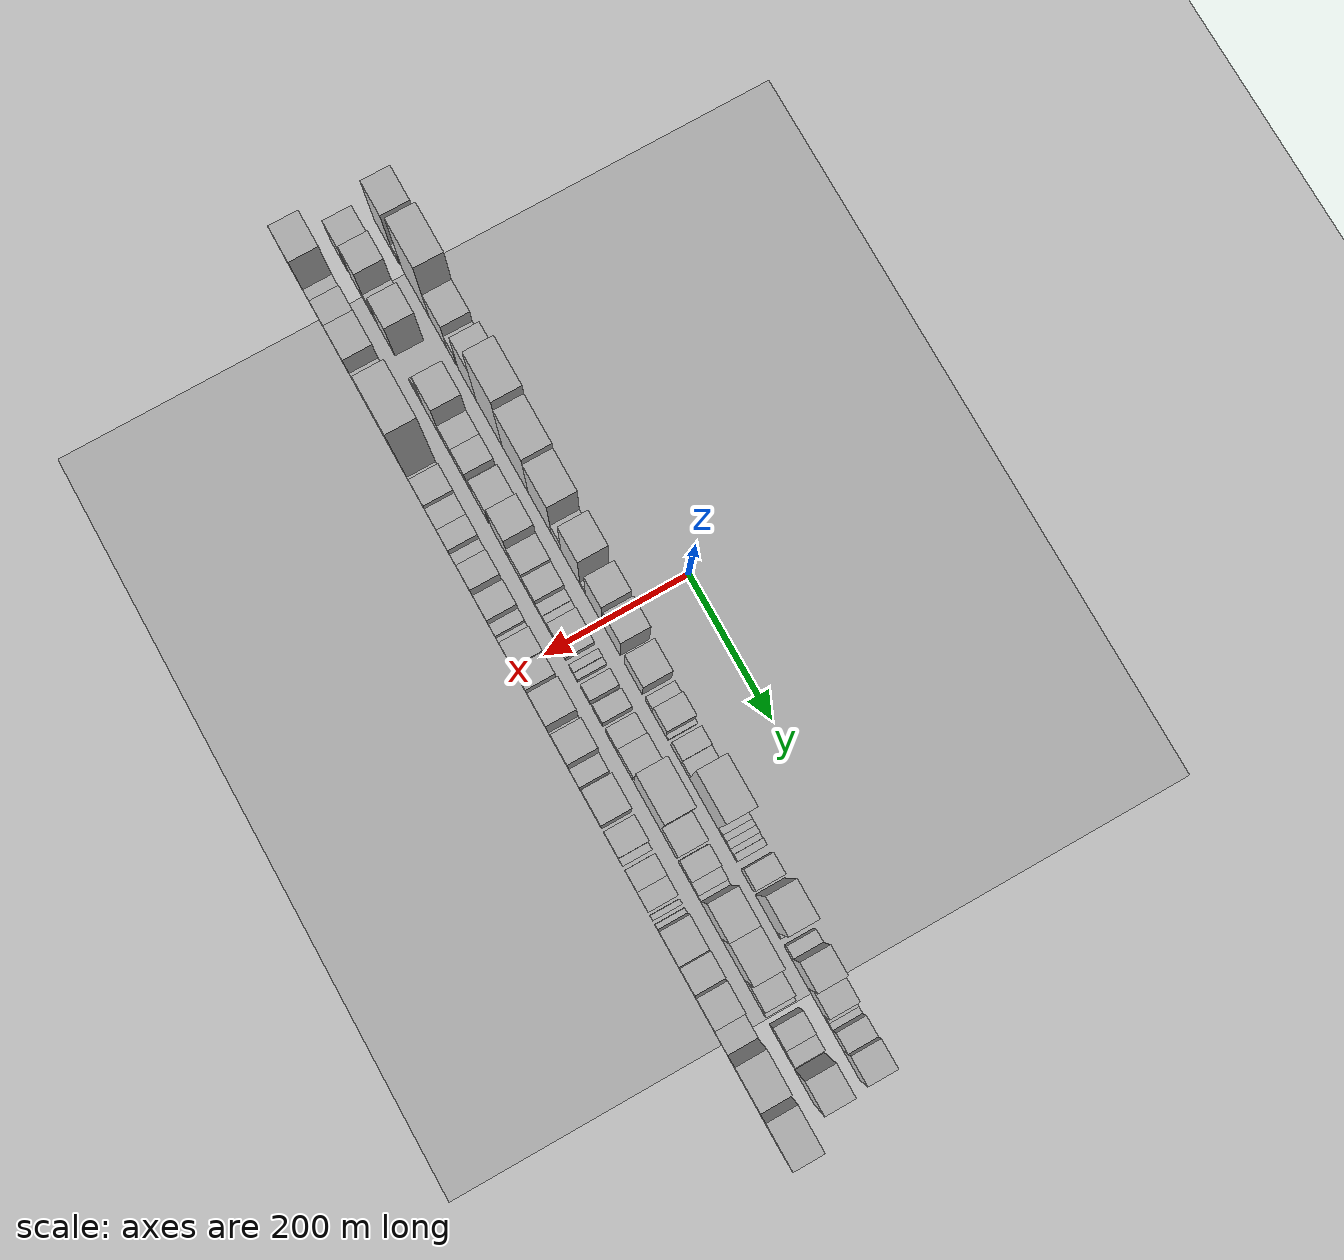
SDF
<?xml version="1.0" encoding="utf-8"?>

<sdf version="1.6">

   <world name="default">

      <gui fullscreen="0">

         <camera name="user_camera">

            <pose>-15 0 4.57585 0 0 0</pose>

            <view_controller>orbit</view_controller>

         </camera>

      </gui>

      <scene>

         <sky>

           <clouds>

             <speed>12</speed>

           </clouds>

         </sky>

         <ambient>0.4 0.4 0.4 1</ambient>

         <background>0.7 0.7 0.7 1</background>

         <shadows>1</shadows>

      </scene>

      <gravity>0 0 -9.8066</gravity>

      <magnetic_field>6e-06 2.3e-05 -4.2e-05</magnetic_field>

      <physics default="0" name="default_physics" type="ode">

         <ode>

            <solver>

               <type>quick</type>

               <iters>10</iters>

               <sor>1.0</sor>

               <use_dynamic_moi_rescaling>0</use_dynamic_moi_rescaling>

            </solver>

            <constraints>

               <cfm>0</cfm>

               <erp>0.2</erp>

               <contact_max_correcting_vel>100</contact_max_correcting_vel>

               <contact_surface_layer>0.001</contact_surface_layer>

            </constraints>

         </ode>

         <max_step_size>0.004</max_step_size>

         <real_time_factor>1</real_time_factor>

         <real_time_update_rate>250</real_time_update_rate>

      </physics>

      <light name="sun" type="directional">

         <cast_shadows>1</cast_shadows>

         <pose>0 0 10 0 0 0</pose>

         <diffuse>0.8 0.8 0.8 1</diffuse>

         <specular>0.2 0.2 0.2 1</specular>

         <attenuation>

            <range>1000</range>

            <constant>0.9</constant>

            <linear>0.01</linear>

            <quadratic>0.001</quadratic>

         </attenuation>

         <direction>-0.5 0.1 -0.9</direction>

      </light>

      <include>

         <name>ground_plane_1</name>

         <uri>model://HANNAS_ground_plane</uri>

         <pose>0 0 0  0 0 0</pose>

      </include>

      <include>

         <name>ground_plane_2</name>

         <uri>model://HANNAS_ground_plane</uri>

         <pose>100 0 0  0 0 0</pose>

      </include>

      <model name="building_1">

         <static>1</static>

         <pose frame="">100.0000 -555.3121 0 0.000000 0.000000 0.000000</pose>

         <link name="link">

            <pose frame="">0 0 63.00 0 0 0</pose>

            <collision name="collision">

               <geometry>

                  <box>

                     <size>40.0000 49.3757 126.0000</size>

                  </box>

               </geometry>

               <max_contacts>10</max_contacts>

               <surface>

                  <contact>

                     <ode/>

                  </contact>

                  <bounce/>

                  <friction>

                     <torsional>

                        <ode/>

                     </torsional>

                     <ode/>

                  </friction>

               </surface>

            </collision>

            <visual name="visual">

               <cast_shadows>0</cast_shadows>

               <geometry>

                  <box>

                     <size>40.0000 49.3757 126.0000</size>

                  </box>

               </geometry>

               <material>

                  <script>

                     <uri>model://HANNAS_wall/materials/scripts</uri>

                     <uri>model://HANNAS_wall/materials/textures</uri>

                     <name>vrc/HANNAS_wall</name>

                  </script>

               </material>

            </visual>

            <self_collide>0</self_collide>

            <enable_wind>0</enable_wind>

            <kinematic>0</kinematic>

         </link>

      </model>

      <model name="building_2">

         <static>1</static>

         <pose frame="">100.0000 -522.3731 0 0.000000 0.000000 0.000000</pose>

         <link name="link">

            <pose frame="">0 0 15.00 0 0 0</pose>

            <collision name="collision">

               <geometry>

                  <box>

                     <size>40.0000 16.5024 30.0000</size>

                  </box>

               </geometry>

               <max_contacts>10</max_contacts>

               <surface>

                  <contact>

                     <ode/>

                  </contact>

                  <bounce/>

                  <friction>

                     <torsional>

                        <ode/>

                     </torsional>

                     <ode/>

                  </friction>

               </surface>

            </collision>

            <visual name="visual">

               <cast_shadows>0</cast_shadows>

               <geometry>

                  <box>

                     <size>40.0000 16.5024 30.0000</size>

                  </box>

               </geometry>

               <material>

                  <script>

                     <uri>model://HANNAS_wall/materials/scripts</uri>

                     <uri>model://HANNAS_wall/materials/textures</uri>

                     <name>vrc/HANNAS_wall</name>

                  </script>

               </material>

            </visual>

            <self_collide>0</self_collide>

            <enable_wind>0</enable_wind>

            <kinematic>0</kinematic>

         </link>

      </model>

      <model name="building_3">

         <static>1</static>

         <pose frame="">100.0000 -470.9707 0 0.000000 0.000000 0.000000</pose>

         <link name="link">

            <pose frame="">0 0 88.50 0 0 0</pose>

            <collision name="collision">

               <geometry>

                  <box>

                     <size>40.0000 68.3023 177.0000</size>

                  </box>

               </geometry>

               <max_contacts>10</max_contacts>

               <surface>

                  <contact>

                     <ode/>

                  </contact>

                  <bounce/>

                  <friction>

                     <torsional>

                        <ode/>

                     </torsional>

                     <ode/>

                  </friction>

               </surface>

            </collision>

            <visual name="visual">

               <cast_shadows>0</cast_shadows>

               <geometry>

                  <box>

                     <size>40.0000 68.3023 177.0000</size>

                  </box>

               </geometry>

               <material>

                  <script>

                     <uri>model://HANNAS_wall/materials/scripts</uri>

                     <uri>model://HANNAS_wall/materials/textures</uri>

                     <name>vrc/HANNAS_wall</name>

                  </script>

               </material>

            </visual>

            <self_collide>0</self_collide>

            <enable_wind>0</enable_wind>

            <kinematic>0</kinematic>

         </link>

      </model>

      <model name="building_4">

         <static>1</static>

         <pose frame="">100.0000 -413.9577 0 0.000000 0.000000 0.000000</pose>

         <link name="link">

            <pose frame="">0 0 42.00 0 0 0</pose>

            <collision name="collision">

               <geometry>

                  <box>

                     <size>40.0000 45.7238 84.0000</size>

                  </box>

               </geometry>

               <max_contacts>10</max_contacts>

               <surface>

                  <contact>

                     <ode/>

                  </contact>

                  <bounce/>

                  <friction>

                     <torsional>

                        <ode/>

                     </torsional>

                     <ode/>

                  </friction>

               </surface>

            </collision>

            <visual name="visual">

               <cast_shadows>0</cast_shadows>

               <geometry>

                  <box>

                     <size>40.0000 45.7238 84.0000</size>

                  </box>

               </geometry>

               <material>

                  <script>

                     <uri>model://HANNAS_wall/materials/scripts</uri>

                     <uri>model://HANNAS_wall/materials/textures</uri>

                     <name>vrc/HANNAS_wall</name>

                  </script>

               </material>

            </visual>

            <self_collide>0</self_collide>

            <enable_wind>0</enable_wind>

            <kinematic>0</kinematic>

         </link>

      </model>

      <model name="building_5">

         <static>1</static>

         <pose frame="">100.0000 -378.4244 0 0.000000 0.000000 0.000000</pose>

         <link name="link">

            <pose frame="">0 0 24.00 0 0 0</pose>

            <collision name="collision">

               <geometry>

                  <box>

                     <size>40.0000 25.3428 48.0000</size>

                  </box>

               </geometry>

               <max_contacts>10</max_contacts>

               <surface>

                  <contact>

                     <ode/>

                  </contact>

                  <bounce/>

                  <friction>

                     <torsional>

                        <ode/>

                     </torsional>

                     <ode/>

                  </friction>

               </surface>

            </collision>

            <visual name="visual">

               <cast_shadows>0</cast_shadows>

               <geometry>

                  <box>

                     <size>40.0000 25.3428 48.0000</size>

                  </box>

               </geometry>

               <material>

                  <script>

                     <uri>model://HANNAS_wall/materials/scripts</uri>

                     <uri>model://HANNAS_wall/materials/textures</uri>

                     <name>vrc/HANNAS_wall</name>

                  </script>

               </material>

            </visual>

            <self_collide>0</self_collide>

            <enable_wind>0</enable_wind>

            <kinematic>0</kinematic>

         </link>

      </model>

      <model name="building_6">

         <static>1</static>

         <pose frame="">100.0000 -337.9833 0 0.000000 0.000000 0.000000</pose>

         <link name="link">

            <pose frame="">0 0 64.50 0 0 0</pose>

            <collision name="collision">

               <geometry>

                  <box>

                     <size>40.0000 45.5393 129.0000</size>

                  </box>

               </geometry>

               <max_contacts>10</max_contacts>

               <surface>

                  <contact>

                     <ode/>

                  </contact>

                  <bounce/>

                  <friction>

                     <torsional>

                        <ode/>

                     </torsional>

                     <ode/>

                  </friction>

               </surface>

            </collision>

            <visual name="visual">

               <cast_shadows>0</cast_shadows>

               <geometry>

                  <box>

                     <size>40.0000 45.5393 129.0000</size>

                  </box>

               </geometry>

               <material>

                  <script>

                     <uri>model://HANNAS_wall/materials/scripts</uri>

                     <uri>model://HANNAS_wall/materials/textures</uri>

                     <name>vrc/HANNAS_wall</name>

                  </script>

               </material>

            </visual>

            <self_collide>0</self_collide>

            <enable_wind>0</enable_wind>

            <kinematic>0</kinematic>

         </link>

      </model>

      <model name="building_7">

         <static>1</static>

         <pose frame="">100.0000 -282.1577 0 0.000000 0.000000 0.000000</pose>

         <link name="link">

            <pose frame="">0 0 102.00 0 0 0</pose>

            <collision name="collision">

               <geometry>

                  <box>

                     <size>40.0000 66.1120 204.0000</size>

                  </box>

               </geometry>

               <max_contacts>10</max_contacts>

               <surface>

                  <contact>

                     <ode/>

                  </contact>

                  <bounce/>

                  <friction>

                     <torsional>

                        <ode/>

                     </torsional>

                     <ode/>

                  </friction>

               </surface>

            </collision>

            <visual name="visual">

               <cast_shadows>0</cast_shadows>

               <geometry>

                  <box>

                     <size>40.0000 66.1120 204.0000</size>

                  </box>

               </geometry>

               <material>

                  <script>

                     <uri>model://HANNAS_wall/materials/scripts</uri>

                     <uri>model://HANNAS_wall/materials/textures</uri>

                     <name>vrc/HANNAS_wall</name>

                  </script>

               </material>

            </visual>

            <self_collide>0</self_collide>

            <enable_wind>0</enable_wind>

            <kinematic>0</kinematic>

         </link>

      </model>

      <model name="building_8">

         <static>1</static>

         <pose frame="">100.0000 -216.1308 0 0.000000 0.000000 0.000000</pose>

         <link name="link">

            <pose frame="">0 0 85.50 0 0 0</pose>

            <collision name="collision">

               <geometry>

                  <box>

                     <size>40.0000 65.9419 171.0000</size>

                  </box>

               </geometry>

               <max_contacts>10</max_contacts>

               <surface>

                  <contact>

                     <ode/>

                  </contact>

                  <bounce/>

                  <friction>

                     <torsional>

                        <ode/>

                     </torsional>

                     <ode/>

                  </friction>

               </surface>

            </collision>

            <visual name="visual">

               <cast_shadows>0</cast_shadows>

               <geometry>

                  <box>

                     <size>40.0000 65.9419 171.0000</size>

                  </box>

               </geometry>

               <material>

                  <script>

                     <uri>model://HANNAS_wall/materials/scripts</uri>

                     <uri>model://HANNAS_wall/materials/textures</uri>

                     <name>vrc/HANNAS_wall</name>

                  </script>

               </material>

            </visual>

            <self_collide>0</self_collide>

            <enable_wind>0</enable_wind>

            <kinematic>0</kinematic>

         </link>

      </model>

      <model name="building_9">

         <static>1</static>

         <pose frame="">100.0000 -154.5169 0 0.000000 0.000000 0.000000</pose>

         <link name="link">

            <pose frame="">0 0 75.00 0 0 0</pose>

            <collision name="collision">

               <geometry>

                  <box>

                     <size>40.0000 57.2859 150.0000</size>

                  </box>

               </geometry>

               <max_contacts>10</max_contacts>

               <surface>

                  <contact>

                     <ode/>

                  </contact>

                  <bounce/>

                  <friction>

                     <torsional>

                        <ode/>

                     </torsional>

                     <ode/>

                  </friction>

               </surface>

            </collision>

            <visual name="visual">

               <cast_shadows>0</cast_shadows>

               <geometry>

                  <box>

                     <size>40.0000 57.2859 150.0000</size>

                  </box>

               </geometry>

               <material>

                  <script>

                     <uri>model://HANNAS_wall/materials/scripts</uri>

                     <uri>model://HANNAS_wall/materials/textures</uri>

                     <name>vrc/HANNAS_wall</name>

                  </script>

               </material>

            </visual>

            <self_collide>0</self_collide>

            <enable_wind>0</enable_wind>

            <kinematic>0</kinematic>

         </link>

      </model>

      <model name="building_10">

         <static>1</static>

         <pose frame="">100.0000 -113.4547 0 0.000000 0.000000 0.000000</pose>

         <link name="link">

            <pose frame="">0 0 24.00 0 0 0</pose>

            <collision name="collision">

               <geometry>

                  <box>

                     <size>40.0000 24.8384 48.0000</size>

                  </box>

               </geometry>

               <max_contacts>10</max_contacts>

               <surface>

                  <contact>

                     <ode/>

                  </contact>

                  <bounce/>

                  <friction>

                     <torsional>

                        <ode/>

                     </torsional>

                     <ode/>

                  </friction>

               </surface>

            </collision>

            <visual name="visual">

               <cast_shadows>0</cast_shadows>

               <geometry>

                  <box>

                     <size>40.0000 24.8384 48.0000</size>

                  </box>

               </geometry>

               <material>

                  <script>

                     <uri>model://HANNAS_wall/materials/scripts</uri>

                     <uri>model://HANNAS_wall/materials/textures</uri>

                     <name>vrc/HANNAS_wall</name>

                  </script>

               </material>

            </visual>

            <self_collide>0</self_collide>

            <enable_wind>0</enable_wind>

            <kinematic>0</kinematic>

         </link>

      </model>

      <model name="building_11">

         <static>1</static>

         <pose frame="">100.0000 -77.6060 0 0.000000 0.000000 0.000000</pose>

         <link name="link">

            <pose frame="">0 0 75.00 0 0 0</pose>

            <collision name="collision">

               <geometry>

                  <box>

                     <size>40.0000 46.8589 150.0000</size>

                  </box>

               </geometry>

               <max_contacts>10</max_contacts>

               <surface>

                  <contact>

                     <ode/>

                  </contact>

                  <bounce/>

                  <friction>

                     <torsional>

                        <ode/>

                     </torsional>

                     <ode/>

                  </friction>

               </surface>

            </collision>

            <visual name="visual">

               <cast_shadows>0</cast_shadows>

               <geometry>

                  <box>

                     <size>40.0000 46.8589 150.0000</size>

                  </box>

               </geometry>

               <material>

                  <script>

                     <uri>model://HANNAS_wall/materials/scripts</uri>

                     <uri>model://HANNAS_wall/materials/textures</uri>

                     <name>vrc/HANNAS_wall</name>

                  </script>

               </material>

            </visual>

            <self_collide>0</self_collide>

            <enable_wind>0</enable_wind>

            <kinematic>0</kinematic>

         </link>

      </model>

      <model name="building_12">

         <static>1</static>

         <pose frame="">100.0000 -50.6539 0 0.000000 0.000000 0.000000</pose>

         <link name="link">

            <pose frame="">0 0 7.50 0 0 0</pose>

            <collision name="collision">

               <geometry>

                  <box>

                     <size>40.0000 7.0453 15.0000</size>

                  </box>

               </geometry>

               <max_contacts>10</max_contacts>

               <surface>

                  <contact>

                     <ode/>

                  </contact>

                  <bounce/>

                  <friction>

                     <torsional>

                        <ode/>

                     </torsional>

                     <ode/>

                  </friction>

               </surface>

            </collision>

            <visual name="visual">

               <cast_shadows>0</cast_shadows>

               <geometry>

                  <box>

                     <size>40.0000 7.0453 15.0000</size>

                  </box>

               </geometry>

               <material>

                  <script>

                     <uri>model://HANNAS_wall/materials/scripts</uri>

                     <uri>model://HANNAS_wall/materials/textures</uri>

                     <name>vrc/HANNAS_wall</name>

                  </script>

               </material>

            </visual>

            <self_collide>0</self_collide>

            <enable_wind>0</enable_wind>

            <kinematic>0</kinematic>

         </link>

      </model>

      <model name="building_13">

         <static>1</static>

         <pose frame="">100.0000 -43.9323 0 0.000000 0.000000 0.000000</pose>

         <link name="link">

            <pose frame="">0 0 7.50 0 0 0</pose>

            <collision name="collision">

               <geometry>

                  <box>

                     <size>40.0000 6.3979 15.0000</size>

                  </box>

               </geometry>

               <max_contacts>10</max_contacts>

               <surface>

                  <contact>

                     <ode/>

                  </contact>

                  <bounce/>

                  <friction>

                     <torsional>

                        <ode/>

                     </torsional>

                     <ode/>

                  </friction>

               </surface>

            </collision>

            <visual name="visual">

               <cast_shadows>0</cast_shadows>

               <geometry>

                  <box>

                     <size>40.0000 6.3979 15.0000</size>

                  </box>

               </geometry>

               <material>

                  <script>

                     <uri>model://HANNAS_wall/materials/scripts</uri>

                     <uri>model://HANNAS_wall/materials/textures</uri>

                     <name>vrc/HANNAS_wall</name>

                  </script>

               </material>

            </visual>

            <self_collide>0</self_collide>

            <enable_wind>0</enable_wind>

            <kinematic>0</kinematic>

         </link>

      </model>

      <model name="building_14">

         <static>1</static>

         <pose frame="">100.0000 -20.3812 0 0.000000 0.000000 0.000000</pose>

         <link name="link">

            <pose frame="">0 0 61.50 0 0 0</pose>

            <collision name="collision">

               <geometry>

                  <box>

                     <size>40.0000 40.7043 123.0000</size>

                  </box>

               </geometry>

               <max_contacts>10</max_contacts>

               <surface>

                  <contact>

                     <ode/>

                  </contact>

                  <bounce/>

                  <friction>

                     <torsional>

                        <ode/>

                     </torsional>

                     <ode/>

                  </friction>

               </surface>

            </collision>

            <visual name="visual">

               <cast_shadows>0</cast_shadows>

               <geometry>

                  <box>

                     <size>40.0000 40.7043 123.0000</size>

                  </box>

               </geometry>

               <material>

                  <script>

                     <uri>model://HANNAS_wall/materials/scripts</uri>

                     <uri>model://HANNAS_wall/materials/textures</uri>

                     <name>vrc/HANNAS_wall</name>

                  </script>

               </material>

            </visual>

            <self_collide>0</self_collide>

            <enable_wind>0</enable_wind>

            <kinematic>0</kinematic>

         </link>

      </model>

      <model name="building_15">

         <static>1</static>

         <pose frame="">100.0000 24.4911 0 0.000000 0.000000 0.000000</pose>

         <link name="link">

            <pose frame="">0 0 55.50 0 0 0</pose>

            <collision name="collision">

               <geometry>

                  <box>

                     <size>40.0000 41.0403 111.0000</size>

                  </box>

               </geometry>

               <max_contacts>10</max_contacts>

               <surface>

                  <contact>

                     <ode/>

                  </contact>

                  <bounce/>

                  <friction>

                     <torsional>

                        <ode/>

                     </torsional>

                     <ode/>

                  </friction>

               </surface>

            </collision>

            <visual name="visual">

               <cast_shadows>0</cast_shadows>

               <geometry>

                  <box>

                     <size>40.0000 41.0403 111.0000</size>

                  </box>

               </geometry>

               <material>

                  <script>

                     <uri>model://HANNAS_wall/materials/scripts</uri>

                     <uri>model://HANNAS_wall/materials/textures</uri>

                     <name>vrc/HANNAS_wall</name>

                  </script>

               </material>

            </visual>

            <self_collide>0</self_collide>

            <enable_wind>0</enable_wind>

            <kinematic>0</kinematic>

         </link>

      </model>

      <model name="building_16">

         <static>1</static>

         <pose frame="">100.0000 76.8772 0 0.000000 0.000000 0.000000</pose>

         <link name="link">

            <pose frame="">0 0 39.00 0 0 0</pose>

            <collision name="collision">

               <geometry>

                  <box>

                     <size>40.0000 43.7319 78.0000</size>

                  </box>

               </geometry>

               <max_contacts>10</max_contacts>

               <surface>

                  <contact>

                     <ode/>

                  </contact>

                  <bounce/>

                  <friction>

                     <torsional>

                        <ode/>

                     </torsional>

                     <ode/>

                  </friction>

               </surface>

            </collision>

            <visual name="visual">

               <cast_shadows>0</cast_shadows>

               <geometry>

                  <box>

                     <size>40.0000 43.7319 78.0000</size>

                  </box>

               </geometry>

               <material>

                  <script>

                     <uri>model://HANNAS_wall/materials/scripts</uri>

                     <uri>model://HANNAS_wall/materials/textures</uri>

                     <name>vrc/HANNAS_wall</name>

                  </script>

               </material>

            </visual>

            <self_collide>0</self_collide>

            <enable_wind>0</enable_wind>

            <kinematic>0</kinematic>

         </link>

      </model>

      <model name="building_17">

         <static>1</static>

         <pose frame="">100.0000 114.5624 0 0.000000 0.000000 0.000000</pose>

         <link name="link">

            <pose frame="">0 0 16.50 0 0 0</pose>

            <collision name="collision">

               <geometry>

                  <box>

                     <size>40.0000 17.6386 33.0000</size>

                  </box>

               </geometry>

               <max_contacts>10</max_contacts>

               <surface>

                  <contact>

                     <ode/>

                  </contact>

                  <bounce/>

                  <friction>

                     <torsional>

                        <ode/>

                     </torsional>

                     <ode/>

                  </friction>

               </surface>

            </collision>

            <visual name="visual">

               <cast_shadows>0</cast_shadows>

               <geometry>

                  <box>

                     <size>40.0000 17.6386 33.0000</size>

                  </box>

               </geometry>

               <material>

                  <script>

                     <uri>model://HANNAS_wall/materials/scripts</uri>

                     <uri>model://HANNAS_wall/materials/textures</uri>

                     <name>vrc/HANNAS_wall</name>

                  </script>

               </material>

            </visual>

            <self_collide>0</self_collide>

            <enable_wind>0</enable_wind>

            <kinematic>0</kinematic>

         </link>

      </model>

      <model name="building_18">

         <static>1</static>

         <pose frame="">100.0000 139.4143 0 0.000000 0.000000 0.000000</pose>

         <link name="link">

            <pose frame="">0 0 30.00 0 0 0</pose>

            <collision name="collision">

               <geometry>

                  <box>

                     <size>40.0000 32.0651 60.0000</size>

                  </box>

               </geometry>

               <max_contacts>10</max_contacts>

               <surface>

                  <contact>

                     <ode/>

                  </contact>

                  <bounce/>

                  <friction>

                     <torsional>

                        <ode/>

                     </torsional>

                     <ode/>

                  </friction>

               </surface>

            </collision>

            <visual name="visual">

               <cast_shadows>0</cast_shadows>

               <geometry>

                  <box>

                     <size>40.0000 32.0651 60.0000</size>

                  </box>

               </geometry>

               <material>

                  <script>

                     <uri>model://HANNAS_wall/materials/scripts</uri>

                     <uri>model://HANNAS_wall/materials/textures</uri>

                     <name>vrc/HANNAS_wall</name>

                  </script>

               </material>

            </visual>

            <self_collide>0</self_collide>

            <enable_wind>0</enable_wind>

            <kinematic>0</kinematic>

         </link>

      </model>

      <model name="building_19">

         <static>1</static>

         <pose frame="">100.0000 158.6503 0 0.000000 0.000000 0.000000</pose>

         <link name="link">

            <pose frame="">0 0 7.50 0 0 0</pose>

            <collision name="collision">

               <geometry>

                  <box>

                     <size>40.0000 6.4071 15.0000</size>

                  </box>

               </geometry>

               <max_contacts>10</max_contacts>

               <surface>

                  <contact>

                     <ode/>

                  </contact>

                  <bounce/>

                  <friction>

                     <torsional>

                        <ode/>

                     </torsional>

                     <ode/>

                  </friction>

               </surface>

            </collision>

            <visual name="visual">

               <cast_shadows>0</cast_shadows>

               <geometry>

                  <box>

                     <size>40.0000 6.4071 15.0000</size>

                  </box>

               </geometry>

               <material>

                  <script>

                     <uri>model://HANNAS_wall/materials/scripts</uri>

                     <uri>model://HANNAS_wall/materials/textures</uri>

                     <name>vrc/HANNAS_wall</name>

                  </script>

               </material>

            </visual>

            <self_collide>0</self_collide>

            <enable_wind>0</enable_wind>

            <kinematic>0</kinematic>

         </link>

      </model>

      <model name="building_20">

         <static>1</static>

         <pose frame="">100.0000 180.4715 0 0.000000 0.000000 0.000000</pose>

         <link name="link">

            <pose frame="">0 0 24.00 0 0 0</pose>

            <collision name="collision">

               <geometry>

                  <box>

                     <size>40.0000 25.2353 48.0000</size>

                  </box>

               </geometry>

               <max_contacts>10</max_contacts>

               <surface>

                  <contact>

                     <ode/>

                  </contact>

                  <bounce/>

                  <friction>

                     <torsional>

                        <ode/>

                     </torsional>

                     <ode/>

                  </friction>

               </surface>

            </collision>

            <visual name="visual">

               <cast_shadows>0</cast_shadows>

               <geometry>

                  <box>

                     <size>40.0000 25.2353 48.0000</size>

                  </box>

               </geometry>

               <material>

                  <script>

                     <uri>model://HANNAS_wall/materials/scripts</uri>

                     <uri>model://HANNAS_wall/materials/textures</uri>

                     <name>vrc/HANNAS_wall</name>

                  </script>

               </material>

            </visual>

            <self_collide>0</self_collide>

            <enable_wind>0</enable_wind>

            <kinematic>0</kinematic>

         </link>

      </model>

      <model name="building_21">

         <static>1</static>

         <pose frame="">100.0000 203.3106 0 0.000000 0.000000 0.000000</pose>

         <link name="link">

            <pose frame="">0 0 18.00 0 0 0</pose>

            <collision name="collision">

               <geometry>

                  <box>

                     <size>40.0000 20.4430 36.0000</size>

                  </box>

               </geometry>

               <max_contacts>10</max_contacts>

               <surface>

                  <contact>

                     <ode/>

                  </contact>

                  <bounce/>

                  <friction>

                     <torsional>

                        <ode/>

                     </torsional>

                     <ode/>

                  </friction>

               </surface>

            </collision>

            <visual name="visual">

               <cast_shadows>0</cast_shadows>

               <geometry>

                  <box>

                     <size>40.0000 20.4430 36.0000</size>

                  </box>

               </geometry>

               <material>

                  <script>

                     <uri>model://HANNAS_wall/materials/scripts</uri>

                     <uri>model://HANNAS_wall/materials/textures</uri>

                     <name>vrc/HANNAS_wall</name>

                  </script>

               </material>

            </visual>

            <self_collide>0</self_collide>

            <enable_wind>0</enable_wind>

            <kinematic>0</kinematic>

         </link>

      </model>

      <model name="building_22">

         <static>1</static>

         <pose frame="">100.0000 247.0963 0 0.000000 0.000000 0.000000</pose>

         <link name="link">

            <pose frame="">0 0 84.00 0 0 0</pose>

            <collision name="collision">

               <geometry>

                  <box>

                     <size>40.0000 67.1283 168.0000</size>

                  </box>

               </geometry>

               <max_contacts>10</max_contacts>

               <surface>

                  <contact>

                     <ode/>

                  </contact>

                  <bounce/>

                  <friction>

                     <torsional>

                        <ode/>

                     </torsional>

                     <ode/>

                  </friction>

               </surface>

            </collision>

            <visual name="visual">

               <cast_shadows>0</cast_shadows>

               <geometry>

                  <box>

                     <size>40.0000 67.1283 168.0000</size>

                  </box>

               </geometry>

               <material>

                  <script>

                     <uri>model://HANNAS_wall/materials/scripts</uri>

                     <uri>model://HANNAS_wall/materials/textures</uri>

                     <name>vrc/HANNAS_wall</name>

                  </script>

               </material>

            </visual>

            <self_collide>0</self_collide>

            <enable_wind>0</enable_wind>

            <kinematic>0</kinematic>

         </link>

      </model>

      <model name="building_23">

         <static>1</static>

         <pose frame="">100.0000 285.5827 0 0.000000 0.000000 0.000000</pose>

         <link name="link">

            <pose frame="">0 0 10.50 0 0 0</pose>

            <collision name="collision">

               <geometry>

                  <box>

                     <size>40.0000 9.8445 21.0000</size>

                  </box>

               </geometry>

               <max_contacts>10</max_contacts>

               <surface>

                  <contact>

                     <ode/>

                  </contact>

                  <bounce/>

                  <friction>

                     <torsional>

                        <ode/>

                     </torsional>

                     <ode/>

                  </friction>

               </surface>

            </collision>

            <visual name="visual">

               <cast_shadows>0</cast_shadows>

               <geometry>

                  <box>

                     <size>40.0000 9.8445 21.0000</size>

                  </box>

               </geometry>

               <material>

                  <script>

                     <uri>model://HANNAS_wall/materials/scripts</uri>

                     <uri>model://HANNAS_wall/materials/textures</uri>

                     <name>vrc/HANNAS_wall</name>

                  </script>

               </material>

            </visual>

            <self_collide>0</self_collide>

            <enable_wind>0</enable_wind>

            <kinematic>0</kinematic>

         </link>

      </model>

      <model name="building_24">

         <static>1</static>

         <pose frame="">100.0000 294.8007 0 0.000000 0.000000 0.000000</pose>

         <link name="link">

            <pose frame="">0 0 10.50 0 0 0</pose>

            <collision name="collision">

               <geometry>

                  <box>

                     <size>40.0000 8.5914 21.0000</size>

                  </box>

               </geometry>

               <max_contacts>10</max_contacts>

               <surface>

                  <contact>

                     <ode/>

                  </contact>

                  <bounce/>

                  <friction>

                     <torsional>

                        <ode/>

                     </torsional>

                     <ode/>

                  </friction>

               </surface>

            </collision>

            <visual name="visual">

               <cast_shadows>0</cast_shadows>

               <geometry>

                  <box>

                     <size>40.0000 8.5914 21.0000</size>

                  </box>

               </geometry>

               <material>

                  <script>

                     <uri>model://HANNAS_wall/materials/scripts</uri>

                     <uri>model://HANNAS_wall/materials/textures</uri>

                     <name>vrc/HANNAS_wall</name>

                  </script>

               </material>

            </visual>

            <self_collide>0</self_collide>

            <enable_wind>0</enable_wind>

            <kinematic>0</kinematic>

         </link>

      </model>

      <model name="building_25">

         <static>1</static>

         <pose frame="">100.0000 303.9282 0 0.000000 0.000000 0.000000</pose>

         <link name="link">

            <pose frame="">0 0 10.50 0 0 0</pose>

            <collision name="collision">

               <geometry>

                  <box>

                     <size>40.0000 9.6634 21.0000</size>

                  </box>

               </geometry>

               <max_contacts>10</max_contacts>

               <surface>

                  <contact>

                     <ode/>

                  </contact>

                  <bounce/>

                  <friction>

                     <torsional>

                        <ode/>

                     </torsional>

                     <ode/>

                  </friction>

               </surface>

            </collision>

            <visual name="visual">

               <cast_shadows>0</cast_shadows>

               <geometry>

                  <box>

                     <size>40.0000 9.6634 21.0000</size>

                  </box>

               </geometry>

               <material>

                  <script>

                     <uri>model://HANNAS_wall/materials/scripts</uri>

                     <uri>model://HANNAS_wall/materials/textures</uri>

                     <name>vrc/HANNAS_wall</name>

                  </script>

               </material>

            </visual>

            <self_collide>0</self_collide>

            <enable_wind>0</enable_wind>

            <kinematic>0</kinematic>

         </link>

      </model>

      <model name="building_26">

         <static>1</static>

         <pose frame="">100.0000 312.4724 0 0.000000 0.000000 0.000000</pose>

         <link name="link">

            <pose frame="">0 0 7.50 0 0 0</pose>

            <collision name="collision">

               <geometry>

                  <box>

                     <size>40.0000 7.4251 15.0000</size>

                  </box>

               </geometry>

               <max_contacts>10</max_contacts>

               <surface>

                  <contact>

                     <ode/>

                  </contact>

                  <bounce/>

                  <friction>

                     <torsional>

                        <ode/>

                     </torsional>

                     <ode/>

                  </friction>

               </surface>

            </collision>

            <visual name="visual">

               <cast_shadows>0</cast_shadows>

               <geometry>

                  <box>

                     <size>40.0000 7.4251 15.0000</size>

                  </box>

               </geometry>

               <material>

                  <script>

                     <uri>model://HANNAS_wall/materials/scripts</uri>

                     <uri>model://HANNAS_wall/materials/textures</uri>

                     <name>vrc/HANNAS_wall</name>

                  </script>

               </material>

            </visual>

            <self_collide>0</self_collide>

            <enable_wind>0</enable_wind>

            <kinematic>0</kinematic>

         </link>

      </model>

      <model name="building_27">

         <static>1</static>

         <pose frame="">100.0000 320.8643 0 0.000000 0.000000 0.000000</pose>

         <link name="link">

            <pose frame="">0 0 10.50 0 0 0</pose>

            <collision name="collision">

               <geometry>

                  <box>

                     <size>40.0000 9.3586 21.0000</size>

                  </box>

               </geometry>

               <max_contacts>10</max_contacts>

               <surface>

                  <contact>

                     <ode/>

                  </contact>

                  <bounce/>

                  <friction>

                     <torsional>

                        <ode/>

                     </torsional>

                     <ode/>

                  </friction>

               </surface>

            </collision>

            <visual name="visual">

               <cast_shadows>0</cast_shadows>

               <geometry>

                  <box>

                     <size>40.0000 9.3586 21.0000</size>

                  </box>

               </geometry>

               <material>

                  <script>

                     <uri>model://HANNAS_wall/materials/scripts</uri>

                     <uri>model://HANNAS_wall/materials/textures</uri>

                     <name>vrc/HANNAS_wall</name>

                  </script>

               </material>

            </visual>

            <self_collide>0</self_collide>

            <enable_wind>0</enable_wind>

            <kinematic>0</kinematic>

         </link>

      </model>

      <model name="building_28">

         <static>1</static>

         <pose frame="">100.0000 349.8783 0 0.000000 0.000000 0.000000</pose>

         <link name="link">

            <pose frame="">0 0 24.00 0 0 0</pose>

            <collision name="collision">

               <geometry>

                  <box>

                     <size>40.0000 28.6696 48.0000</size>

                  </box>

               </geometry>

               <max_contacts>10</max_contacts>

               <surface>

                  <contact>

                     <ode/>

                  </contact>

                  <bounce/>

                  <friction>

                     <torsional>

                        <ode/>

                     </torsional>

                     <ode/>

                  </friction>

               </surface>

            </collision>

            <visual name="visual">

               <cast_shadows>0</cast_shadows>

               <geometry>

                  <box>

                     <size>40.0000 28.6696 48.0000</size>

                  </box>

               </geometry>

               <material>

                  <script>

                     <uri>model://HANNAS_wall/materials/scripts</uri>

                     <uri>model://HANNAS_wall/materials/textures</uri>

                     <name>vrc/HANNAS_wall</name>

                  </script>

               </material>

            </visual>

            <self_collide>0</self_collide>

            <enable_wind>0</enable_wind>

            <kinematic>0</kinematic>

         </link>

      </model>

      <model name="building_29">

         <static>1</static>

         <pose frame="">100.0000 394.3280 0 0.000000 0.000000 0.000000</pose>

         <link name="link">

            <pose frame="">0 0 73.50 0 0 0</pose>

            <collision name="collision">

               <geometry>

                  <box>

                     <size>40.0000 50.2297 147.0000</size>

                  </box>

               </geometry>

               <max_contacts>10</max_contacts>

               <surface>

                  <contact>

                     <ode/>

                  </contact>

                  <bounce/>

                  <friction>

                     <torsional>

                        <ode/>

                     </torsional>

                     <ode/>

                  </friction>

               </surface>

            </collision>

            <visual name="visual">

               <cast_shadows>0</cast_shadows>

               <geometry>

                  <box>

                     <size>40.0000 50.2297 147.0000</size>

                  </box>

               </geometry>

               <material>

                  <script>

                     <uri>model://HANNAS_wall/materials/scripts</uri>

                     <uri>model://HANNAS_wall/materials/textures</uri>

                     <name>vrc/HANNAS_wall</name>

                  </script>

               </material>

            </visual>

            <self_collide>0</self_collide>

            <enable_wind>0</enable_wind>

            <kinematic>0</kinematic>

         </link>

      </model>

      <model name="building_30">

         <static>1</static>

         <pose frame="">100.0000 423.3391 0 0.000000 0.000000 0.000000</pose>

         <link name="link">

            <pose frame="">0 0 9.00 0 0 0</pose>

            <collision name="collision">

               <geometry>

                  <box>

                     <size>40.0000 7.7924 18.0000</size>

                  </box>

               </geometry>

               <max_contacts>10</max_contacts>

               <surface>

                  <contact>

                     <ode/>

                  </contact>

                  <bounce/>

                  <friction>

                     <torsional>

                        <ode/>

                     </torsional>

                     <ode/>

                  </friction>

               </surface>

            </collision>

            <visual name="visual">

               <cast_shadows>0</cast_shadows>

               <geometry>

                  <box>

                     <size>40.0000 7.7924 18.0000</size>

                  </box>

               </geometry>

               <material>

                  <script>

                     <uri>model://HANNAS_wall/materials/scripts</uri>

                     <uri>model://HANNAS_wall/materials/textures</uri>

                     <name>vrc/HANNAS_wall</name>

                  </script>

               </material>

            </visual>

            <self_collide>0</self_collide>

            <enable_wind>0</enable_wind>

            <kinematic>0</kinematic>

         </link>

      </model>

      <model name="building_31">

         <static>1</static>

         <pose frame="">100.0000 444.5857 0 0.000000 0.000000 0.000000</pose>

         <link name="link">

            <pose frame="">0 0 16.50 0 0 0</pose>

            <collision name="collision">

               <geometry>

                  <box>

                     <size>40.0000 16.7009 33.0000</size>

                  </box>

               </geometry>

               <max_contacts>10</max_contacts>

               <surface>

                  <contact>

                     <ode/>

                  </contact>

                  <bounce/>

                  <friction>

                     <torsional>

                        <ode/>

                     </torsional>

                     <ode/>

                  </friction>

               </surface>

            </collision>

            <visual name="visual">

               <cast_shadows>0</cast_shadows>

               <geometry>

                  <box>

                     <size>40.0000 16.7009 33.0000</size>

                  </box>

               </geometry>

               <material>

                  <script>

                     <uri>model://HANNAS_wall/materials/scripts</uri>

                     <uri>model://HANNAS_wall/materials/textures</uri>

                     <name>vrc/HANNAS_wall</name>

                  </script>

               </material>

            </visual>

            <self_collide>0</self_collide>

            <enable_wind>0</enable_wind>

            <kinematic>0</kinematic>

         </link>

      </model>

      <model name="building_32">

         <static>1</static>

         <pose frame="">100.0000 472.7256 0 0.000000 0.000000 0.000000</pose>

         <link name="link">

            <pose frame="">0 0 51.00 0 0 0</pose>

            <collision name="collision">

               <geometry>

                  <box>

                     <size>40.0000 39.5789 102.0000</size>

                  </box>

               </geometry>

               <max_contacts>10</max_contacts>

               <surface>

                  <contact>

                     <ode/>

                  </contact>

                  <bounce/>

                  <friction>

                     <torsional>

                        <ode/>

                     </torsional>

                     <ode/>

                  </friction>

               </surface>

            </collision>

            <visual name="visual">

               <cast_shadows>0</cast_shadows>

               <geometry>

                  <box>

                     <size>40.0000 39.5789 102.0000</size>

                  </box>

               </geometry>

               <material>

                  <script>

                     <uri>model://HANNAS_wall/materials/scripts</uri>

                     <uri>model://HANNAS_wall/materials/textures</uri>

                     <name>vrc/HANNAS_wall</name>

                  </script>

               </material>

            </visual>

            <self_collide>0</self_collide>

            <enable_wind>0</enable_wind>

            <kinematic>0</kinematic>

         </link>

      </model>

      <model name="building_33">

         <static>1</static>

         <pose frame="">100.0000 510.2920 0 0.000000 0.000000 0.000000</pose>

         <link name="link">

            <pose frame="">0 0 33.00 0 0 0</pose>

            <collision name="collision">

               <geometry>

                  <box>

                     <size>40.0000 35.5539 66.0000</size>

                  </box>

               </geometry>

               <max_contacts>10</max_contacts>

               <surface>

                  <contact>

                     <ode/>

                  </contact>

                  <bounce/>

                  <friction>

                     <torsional>

                        <ode/>

                     </torsional>

                     <ode/>

                  </friction>

               </surface>

            </collision>

            <visual name="visual">

               <cast_shadows>0</cast_shadows>

               <geometry>

                  <box>

                     <size>40.0000 35.5539 66.0000</size>

                  </box>

               </geometry>

               <material>

                  <script>

                     <uri>model://HANNAS_wall/materials/scripts</uri>

                     <uri>model://HANNAS_wall/materials/textures</uri>

                     <name>vrc/HANNAS_wall</name>

                  </script>

               </material>

            </visual>

            <self_collide>0</self_collide>

            <enable_wind>0</enable_wind>

            <kinematic>0</kinematic>

         </link>

      </model>

      <model name="building_34">

         <static>1</static>

         <pose frame="">100.0000 532.7172 0 0.000000 0.000000 0.000000</pose>

         <link name="link">

            <pose frame="">0 0 10.50 0 0 0</pose>

            <collision name="collision">

               <geometry>

                  <box>

                     <size>40.0000 9.2965 21.0000</size>

                  </box>

               </geometry>

               <max_contacts>10</max_contacts>

               <surface>

                  <contact>

                     <ode/>

                  </contact>

                  <bounce/>

                  <friction>

                     <torsional>

                        <ode/>

                     </torsional>

                     <ode/>

                  </friction>

               </surface>

            </collision>

            <visual name="visual">

               <cast_shadows>0</cast_shadows>

               <geometry>

                  <box>

                     <size>40.0000 9.2965 21.0000</size>

                  </box>

               </geometry>

               <material>

                  <script>

                     <uri>model://HANNAS_wall/materials/scripts</uri>

                     <uri>model://HANNAS_wall/materials/textures</uri>

                     <name>vrc/HANNAS_wall</name>

                  </script>

               </material>

            </visual>

            <self_collide>0</self_collide>

            <enable_wind>0</enable_wind>

            <kinematic>0</kinematic>

         </link>

      </model>

      <model name="building_35">

         <static>1</static>

         <pose frame="">100.0000 541.8616 0 0.000000 0.000000 0.000000</pose>

         <link name="link">

            <pose frame="">0 0 9.00 0 0 0</pose>

            <collision name="collision">

               <geometry>

                  <box>

                     <size>40.0000 8.9924 18.0000</size>

                  </box>

               </geometry>

               <max_contacts>10</max_contacts>

               <surface>

                  <contact>

                     <ode/>

                  </contact>

                  <bounce/>

                  <friction>

                     <torsional>

                        <ode/>

                     </torsional>

                     <ode/>

                  </friction>

               </surface>

            </collision>

            <visual name="visual">

               <cast_shadows>0</cast_shadows>

               <geometry>

                  <box>

                     <size>40.0000 8.9924 18.0000</size>

                  </box>

               </geometry>

               <material>

                  <script>

                     <uri>model://HANNAS_wall/materials/scripts</uri>

                     <uri>model://HANNAS_wall/materials/textures</uri>

                     <name>vrc/HANNAS_wall</name>

                  </script>

               </material>

            </visual>

            <self_collide>0</self_collide>

            <enable_wind>0</enable_wind>

            <kinematic>0</kinematic>

         </link>

      </model>

      <model name="building_36">

         <static>1</static>

         <pose frame="">100.0000 559.9342 0 0.000000 0.000000 0.000000</pose>

         <link name="link">

            <pose frame="">0 0 24.00 0 0 0</pose>

            <collision name="collision">

               <geometry>

                  <box>

                     <size>40.0000 27.1529 48.0000</size>

                  </box>

               </geometry>

               <max_contacts>10</max_contacts>

               <surface>

                  <contact>

                     <ode/>

                  </contact>

                  <bounce/>

                  <friction>

                     <torsional>

                        <ode/>

                     </torsional>

                     <ode/>

                  </friction>

               </surface>

            </collision>

            <visual name="visual">

               <cast_shadows>0</cast_shadows>

               <geometry>

                  <box>

                     <size>40.0000 27.1529 48.0000</size>

                  </box>

               </geometry>

               <material>

                  <script>

                     <uri>model://HANNAS_wall/materials/scripts</uri>

                     <uri>model://HANNAS_wall/materials/textures</uri>

                     <name>vrc/HANNAS_wall</name>

                  </script>

               </material>

            </visual>

            <self_collide>0</self_collide>

            <enable_wind>0</enable_wind>

            <kinematic>0</kinematic>

         </link>

      </model>

      <model name="building_37">

         <static>1</static>

         <pose frame="">100.0000 592.8155 0 0.000000 0.000000 0.000000</pose>

         <link name="link">

            <pose frame="">0 0 34.50 0 0 0</pose>

            <collision name="collision">

               <geometry>

                  <box>

                     <size>40.0000 38.6096 69.0000</size>

                  </box>

               </geometry>

               <max_contacts>10</max_contacts>

               <surface>

                  <contact>

                     <ode/>

                  </contact>

                  <bounce/>

                  <friction>

                     <torsional>

                        <ode/>

                     </torsional>

                     <ode/>

                  </friction>

               </surface>

            </collision>

            <visual name="visual">

               <cast_shadows>0</cast_shadows>

               <geometry>

                  <box>

                     <size>40.0000 38.6096 69.0000</size>

                  </box>

               </geometry>

               <material>

                  <script>

                     <uri>model://HANNAS_wall/materials/scripts</uri>

                     <uri>model://HANNAS_wall/materials/textures</uri>

                     <name>vrc/HANNAS_wall</name>

                  </script>

               </material>

            </visual>

            <self_collide>0</self_collide>

            <enable_wind>0</enable_wind>

            <kinematic>0</kinematic>

         </link>

      </model>

      <model name="building_38">

         <static>1</static>

         <pose frame="">160.0000 -558.5366 0 0.000000 0.000000 0.000000</pose>

         <link name="link">

            <pose frame="">0 0 37.50 0 0 0</pose>

            <collision name="collision">

               <geometry>

                  <box>

                     <size>40.0000 42.9268 75.0000</size>

                  </box>

               </geometry>

               <max_contacts>10</max_contacts>

               <surface>

                  <contact>

                     <ode/>

                  </contact>

                  <bounce/>

                  <friction>

                     <torsional>

                        <ode/>

                     </torsional>

                     <ode/>

                  </friction>

               </surface>

            </collision>

            <visual name="visual">

               <cast_shadows>0</cast_shadows>

               <geometry>

                  <box>

                     <size>40.0000 42.9268 75.0000</size>

                  </box>

               </geometry>

               <material>

                  <script>

                     <uri>model://HANNAS_wall/materials/scripts</uri>

                     <uri>model://HANNAS_wall/materials/textures</uri>

                     <name>vrc/HANNAS_wall</name>

                  </script>

               </material>

            </visual>

            <self_collide>0</self_collide>

            <enable_wind>0</enable_wind>

            <kinematic>0</kinematic>

         </link>

      </model>

      <model name="building_39">

         <static>1</static>

         <pose frame="">160.0000 -508.1155 0 0.000000 0.000000 0.000000</pose>

         <link name="link">

            <pose frame="">0 0 55.50 0 0 0</pose>

            <collision name="collision">

               <geometry>

                  <box>

                     <size>40.0000 39.9153 111.0000</size>

                  </box>

               </geometry>

               <max_contacts>10</max_contacts>

               <surface>

                  <contact>

                     <ode/>

                  </contact>

                  <bounce/>

                  <friction>

                     <torsional>

                        <ode/>

                     </torsional>

                     <ode/>

                  </friction>

               </surface>

            </collision>

            <visual name="visual">

               <cast_shadows>0</cast_shadows>

               <geometry>

                  <box>

                     <size>40.0000 39.9153 111.0000</size>

                  </box>

               </geometry>

               <material>

                  <script>

                     <uri>model://HANNAS_wall/materials/scripts</uri>

                     <uri>model://HANNAS_wall/materials/textures</uri>

                     <name>vrc/HANNAS_wall</name>

                  </script>

               </material>

            </visual>

            <self_collide>0</self_collide>

            <enable_wind>0</enable_wind>

            <kinematic>0</kinematic>

         </link>

      </model>

      <model name="building_40">

         <static>1</static>

         <pose frame="">160.0000 -476.9015 0 0.000000 0.000000 0.000000</pose>

         <link name="link">

            <pose frame="">0 0 19.50 0 0 0</pose>

            <collision name="collision">

               <geometry>

                  <box>

                     <size>40.0000 22.5127 39.0000</size>

                  </box>

               </geometry>

               <max_contacts>10</max_contacts>

               <surface>

                  <contact>

                     <ode/>

                  </contact>

                  <bounce/>

                  <friction>

                     <torsional>

                        <ode/>

                     </torsional>

                     <ode/>

                  </friction>

               </surface>

            </collision>

            <visual name="visual">

               <cast_shadows>0</cast_shadows>

               <geometry>

                  <box>

                     <size>40.0000 22.5127 39.0000</size>

                  </box>

               </geometry>

               <material>

                  <script>

                     <uri>model://HANNAS_wall/materials/scripts</uri>

                     <uri>model://HANNAS_wall/materials/textures</uri>

                     <name>vrc/HANNAS_wall</name>

                  </script>

               </material>

            </visual>

            <self_collide>0</self_collide>

            <enable_wind>0</enable_wind>

            <kinematic>0</kinematic>

         </link>

      </model>

      <model name="building_41">

         <static>1</static>

         <pose frame="">160.0000 -461.2020 0 0.000000 0.000000 0.000000</pose>

         <link name="link">

            <pose frame="">0 0 9.00 0 0 0</pose>

            <collision name="collision">

               <geometry>

                  <box>

                     <size>40.0000 8.8863 18.0000</size>

                  </box>

               </geometry>

               <max_contacts>10</max_contacts>

               <surface>

                  <contact>

                     <ode/>

                  </contact>

                  <bounce/>

                  <friction>

                     <torsional>

                        <ode/>

                     </torsional>

                     <ode/>

                  </friction>

               </surface>

            </collision>

            <visual name="visual">

               <cast_shadows>0</cast_shadows>

               <geometry>

                  <box>

                     <size>40.0000 8.8863 18.0000</size>

                  </box>

               </geometry>

               <material>

                  <script>

                     <uri>model://HANNAS_wall/materials/scripts</uri>

                     <uri>model://HANNAS_wall/materials/textures</uri>

                     <name>vrc/HANNAS_wall</name>

                  </script>

               </material>

            </visual>

            <self_collide>0</self_collide>

            <enable_wind>0</enable_wind>

            <kinematic>0</kinematic>

         </link>

      </model>

      <model name="building_42">

         <static>1</static>

         <pose frame="">160.0000 -435.3343 0 0.000000 0.000000 0.000000</pose>

         <link name="link">

            <pose frame="">0 0 54.00 0 0 0</pose>

            <collision name="collision">

               <geometry>

                  <box>

                     <size>40.0000 42.8492 108.0000</size>

                  </box>

               </geometry>

               <max_contacts>10</max_contacts>

               <surface>

                  <contact>

                     <ode/>

                  </contact>

                  <bounce/>

                  <friction>

                     <torsional>

                        <ode/>

                     </torsional>

                     <ode/>

                  </friction>

               </surface>

            </collision>

            <visual name="visual">

               <cast_shadows>0</cast_shadows>

               <geometry>

                  <box>

                     <size>40.0000 42.8492 108.0000</size>

                  </box>

               </geometry>

               <material>

                  <script>

                     <uri>model://HANNAS_wall/materials/scripts</uri>

                     <uri>model://HANNAS_wall/materials/textures</uri>

                     <name>vrc/HANNAS_wall</name>

                  </script>

               </material>

            </visual>

            <self_collide>0</self_collide>

            <enable_wind>0</enable_wind>

            <kinematic>0</kinematic>

         </link>

      </model>

      <model name="building_43">

         <static>1</static>

         <pose frame="">160.0000 -369.8815 0 0.000000 0.000000 0.000000</pose>

         <link name="link">

            <pose frame="">0 0 10.50 0 0 0</pose>

            <collision name="collision">

               <geometry>

                  <box>

                     <size>40.0000 8.6854 21.0000</size>

                  </box>

               </geometry>

               <max_contacts>10</max_contacts>

               <surface>

                  <contact>

                     <ode/>

                  </contact>

                  <bounce/>

                  <friction>

                     <torsional>

                        <ode/>

                     </torsional>

                     <ode/>

                  </friction>

               </surface>

            </collision>

            <visual name="visual">

               <cast_shadows>0</cast_shadows>

               <geometry>

                  <box>

                     <size>40.0000 8.6854 21.0000</size>

                  </box>

               </geometry>

               <material>

                  <script>

                     <uri>model://HANNAS_wall/materials/scripts</uri>

                     <uri>model://HANNAS_wall/materials/textures</uri>

                     <name>vrc/HANNAS_wall</name>

                  </script>

               </material>

            </visual>

            <self_collide>0</self_collide>

            <enable_wind>0</enable_wind>

            <kinematic>0</kinematic>

         </link>

      </model>

      <model name="building_44">

         <static>1</static>

         <pose frame="">160.0000 -353.2454 0 0.000000 0.000000 0.000000</pose>

         <link name="link">

            <pose frame="">0 0 22.50 0 0 0</pose>

            <collision name="collision">

               <geometry>

                  <box>

                     <size>40.0000 24.5867 45.0000</size>

                  </box>

               </geometry>

               <max_contacts>10</max_contacts>

               <surface>

                  <contact>

                     <ode/>

                  </contact>

                  <bounce/>

                  <friction>

                     <torsional>

                        <ode/>

                     </torsional>

                     <ode/>

                  </friction>

               </surface>

            </collision>

            <visual name="visual">

               <cast_shadows>0</cast_shadows>

               <geometry>

                  <box>

                     <size>40.0000 24.5867 45.0000</size>

                  </box>

               </geometry>

               <material>

                  <script>

                     <uri>model://HANNAS_wall/materials/scripts</uri>

                     <uri>model://HANNAS_wall/materials/textures</uri>

                     <name>vrc/HANNAS_wall</name>

                  </script>

               </material>

            </visual>

            <self_collide>0</self_collide>

            <enable_wind>0</enable_wind>

            <kinematic>0</kinematic>

         </link>

      </model>

      <model name="building_45">

         <static>1</static>

         <pose frame="">160.0000 -317.7670 0 0.000000 0.000000 0.000000</pose>

         <link name="link">

            <pose frame="">0 0 64.50 0 0 0</pose>

            <collision name="collision">

               <geometry>

                  <box>

                     <size>40.0000 46.3700 129.0000</size>

                  </box>

               </geometry>

               <max_contacts>10</max_contacts>

               <surface>

                  <contact>

                     <ode/>

                  </contact>

                  <bounce/>

                  <friction>

                     <torsional>

                        <ode/>

                     </torsional>

                     <ode/>

                  </friction>

               </surface>

            </collision>

            <visual name="visual">

               <cast_shadows>0</cast_shadows>

               <geometry>

                  <box>

                     <size>40.0000 46.3700 129.0000</size>

                  </box>

               </geometry>

               <material>

                  <script>

                     <uri>model://HANNAS_wall/materials/scripts</uri>

                     <uri>model://HANNAS_wall/materials/textures</uri>

                     <name>vrc/HANNAS_wall</name>

                  </script>

               </material>

            </visual>

            <self_collide>0</self_collide>

            <enable_wind>0</enable_wind>

            <kinematic>0</kinematic>

         </link>

      </model>

      <model name="building_46">

         <static>1</static>

         <pose frame="">160.0000 -278.0836 0 0.000000 0.000000 0.000000</pose>

         <link name="link">

            <pose frame="">0 0 30.00 0 0 0</pose>

            <collision name="collision">

               <geometry>

                  <box>

                     <size>40.0000 32.9968 60.0000</size>

                  </box>

               </geometry>

               <max_contacts>10</max_contacts>

               <surface>

                  <contact>

                     <ode/>

                  </contact>

                  <bounce/>

                  <friction>

                     <torsional>

                        <ode/>

                     </torsional>

                     <ode/>

                  </friction>

               </surface>

            </collision>

            <visual name="visual">

               <cast_shadows>0</cast_shadows>

               <geometry>

                  <box>

                     <size>40.0000 32.9968 60.0000</size>

                  </box>

               </geometry>

               <material>

                  <script>

                     <uri>model://HANNAS_wall/materials/scripts</uri>

                     <uri>model://HANNAS_wall/materials/textures</uri>

                     <name>vrc/HANNAS_wall</name>

                  </script>

               </material>

            </visual>

            <self_collide>0</self_collide>

            <enable_wind>0</enable_wind>

            <kinematic>0</kinematic>

         </link>

      </model>

      <model name="building_47">

         <static>1</static>

         <pose frame="">160.0000 -244.3424 0 0.000000 0.000000 0.000000</pose>

         <link name="link">

            <pose frame="">0 0 30.00 0 0 0</pose>

            <collision name="collision">

               <geometry>

                  <box>

                     <size>40.0000 34.4856 60.0000</size>

                  </box>

               </geometry>

               <max_contacts>10</max_contacts>

               <surface>

                  <contact>

                     <ode/>

                  </contact>

                  <bounce/>

                  <friction>

                     <torsional>

                        <ode/>

                     </torsional>

                     <ode/>

                  </friction>

               </surface>

            </collision>

            <visual name="visual">

               <cast_shadows>0</cast_shadows>

               <geometry>

                  <box>

                     <size>40.0000 34.4856 60.0000</size>

                  </box>

               </geometry>

               <material>

                  <script>

                     <uri>model://HANNAS_wall/materials/scripts</uri>

                     <uri>model://HANNAS_wall/materials/textures</uri>

                     <name>vrc/HANNAS_wall</name>

                  </script>

               </material>

            </visual>

            <self_collide>0</self_collide>

            <enable_wind>0</enable_wind>

            <kinematic>0</kinematic>

         </link>

      </model>

      <model name="building_48">

         <static>1</static>

         <pose frame="">160.0000 -221.3875 0 0.000000 0.000000 0.000000</pose>

         <link name="link">

            <pose frame="">0 0 13.50 0 0 0</pose>

            <collision name="collision">

               <geometry>

                  <box>

                     <size>40.0000 11.4244 27.0000</size>

                  </box>

               </geometry>

               <max_contacts>10</max_contacts>

               <surface>

                  <contact>

                     <ode/>

                  </contact>

                  <bounce/>

                  <friction>

                     <torsional>

                        <ode/>

                     </torsional>

                     <ode/>

                  </friction>

               </surface>

            </collision>

            <visual name="visual">

               <cast_shadows>0</cast_shadows>

               <geometry>

                  <box>

                     <size>40.0000 11.4244 27.0000</size>

                  </box>

               </geometry>

               <material>

                  <script>

                     <uri>model://HANNAS_wall/materials/scripts</uri>

                     <uri>model://HANNAS_wall/materials/textures</uri>

                     <name>vrc/HANNAS_wall</name>

                  </script>

               </material>

            </visual>

            <self_collide>0</self_collide>

            <enable_wind>0</enable_wind>

            <kinematic>0</kinematic>

         </link>

      </model>

      <model name="building_49">

         <static>1</static>

         <pose frame="">160.0000 -194.1854 0 0.000000 0.000000 0.000000</pose>

         <link name="link">

            <pose frame="">0 0 36.00 0 0 0</pose>

            <collision name="collision">

               <geometry>

                  <box>

                     <size>40.0000 42.9797 72.0000</size>

                  </box>

               </geometry>

               <max_contacts>10</max_contacts>

               <surface>

                  <contact>

                     <ode/>

                  </contact>

                  <bounce/>

                  <friction>

                     <torsional>

                        <ode/>

                     </torsional>

                     <ode/>

                  </friction>

               </surface>

            </collision>

            <visual name="visual">

               <cast_shadows>0</cast_shadows>

               <geometry>

                  <box>

                     <size>40.0000 42.9797 72.0000</size>

                  </box>

               </geometry>

               <material>

                  <script>

                     <uri>model://HANNAS_wall/materials/scripts</uri>

                     <uri>model://HANNAS_wall/materials/textures</uri>

                     <name>vrc/HANNAS_wall</name>

                  </script>

               </material>

            </visual>

            <self_collide>0</self_collide>

            <enable_wind>0</enable_wind>

            <kinematic>0</kinematic>

         </link>

      </model>

      <model name="building_50">

         <static>1</static>

         <pose frame="">160.0000 -143.6674 0 0.000000 0.000000 0.000000</pose>

         <link name="link">

            <pose frame="">0 0 58.50 0 0 0</pose>

            <collision name="collision">

               <geometry>

                  <box>

                     <size>40.0000 42.0563 117.0000</size>

                  </box>

               </geometry>

               <max_contacts>10</max_contacts>

               <surface>

                  <contact>

                     <ode/>

                  </contact>

                  <bounce/>

                  <friction>

                     <torsional>

                        <ode/>

                     </torsional>

                     <ode/>

                  </friction>

               </surface>

            </collision>

            <visual name="visual">

               <cast_shadows>0</cast_shadows>

               <geometry>

                  <box>

                     <size>40.0000 42.0563 117.0000</size>

                  </box>

               </geometry>

               <material>

                  <script>

                     <uri>model://HANNAS_wall/materials/scripts</uri>

                     <uri>model://HANNAS_wall/materials/textures</uri>

                     <name>vrc/HANNAS_wall</name>

                  </script>

               </material>

            </visual>

            <self_collide>0</self_collide>

            <enable_wind>0</enable_wind>

            <kinematic>0</kinematic>

         </link>

      </model>

      <model name="building_51">

         <static>1</static>

         <pose frame="">160.0000 -104.6968 0 0.000000 0.000000 0.000000</pose>

         <link name="link">

            <pose frame="">0 0 34.50 0 0 0</pose>

            <collision name="collision">

               <geometry>

                  <box>

                     <size>40.0000 35.8851 69.0000</size>

                  </box>

               </geometry>

               <max_contacts>10</max_contacts>

               <surface>

                  <contact>

                     <ode/>

                  </contact>

                  <bounce/>

                  <friction>

                     <torsional>

                        <ode/>

                     </torsional>

                     <ode/>

                  </friction>

               </surface>

            </collision>

            <visual name="visual">

               <cast_shadows>0</cast_shadows>

               <geometry>

                  <box>

                     <size>40.0000 35.8851 69.0000</size>

                  </box>

               </geometry>

               <material>

                  <script>

                     <uri>model://HANNAS_wall/materials/scripts</uri>

                     <uri>model://HANNAS_wall/materials/textures</uri>

                     <name>vrc/HANNAS_wall</name>

                  </script>

               </material>

            </visual>

            <self_collide>0</self_collide>

            <enable_wind>0</enable_wind>

            <kinematic>0</kinematic>

         </link>

      </model>

      <model name="building_52">

         <static>1</static>

         <pose frame="">160.0000 -70.5678 0 0.000000 0.000000 0.000000</pose>

         <link name="link">

            <pose frame="">0 0 27.00 0 0 0</pose>

            <collision name="collision">

               <geometry>

                  <box>

                     <size>40.0000 32.3729 54.0000</size>

                  </box>

               </geometry>

               <max_contacts>10</max_contacts>

               <surface>

                  <contact>

                     <ode/>

                  </contact>

                  <bounce/>

                  <friction>

                     <torsional>

                        <ode/>

                     </torsional>

                     <ode/>

                  </friction>

               </surface>

            </collision>

            <visual name="visual">

               <cast_shadows>0</cast_shadows>

               <geometry>

                  <box>

                     <size>40.0000 32.3729 54.0000</size>

                  </box>

               </geometry>

               <material>

                  <script>

                     <uri>model://HANNAS_wall/materials/scripts</uri>

                     <uri>model://HANNAS_wall/materials/textures</uri>

                     <name>vrc/HANNAS_wall</name>

                  </script>

               </material>

            </visual>

            <self_collide>0</self_collide>

            <enable_wind>0</enable_wind>

            <kinematic>0</kinematic>

         </link>

      </model>

      <model name="building_53">

         <static>1</static>

         <pose frame="">160.0000 -46.2525 0 0.000000 0.000000 0.000000</pose>

         <link name="link">

            <pose frame="">0 0 15.00 0 0 0</pose>

            <collision name="collision">

               <geometry>

                  <box>

                     <size>40.0000 16.2577 30.0000</size>

                  </box>

               </geometry>

               <max_contacts>10</max_contacts>

               <surface>

                  <contact>

                     <ode/>

                  </contact>

                  <bounce/>

                  <friction>

                     <torsional>

                        <ode/>

                     </torsional>

                     <ode/>

                  </friction>

               </surface>

            </collision>

            <visual name="visual">

               <cast_shadows>0</cast_shadows>

               <geometry>

                  <box>

                     <size>40.0000 16.2577 30.0000</size>

                  </box>

               </geometry>

               <material>

                  <script>

                     <uri>model://HANNAS_wall/materials/scripts</uri>

                     <uri>model://HANNAS_wall/materials/textures</uri>

                     <name>vrc/HANNAS_wall</name>

                  </script>

               </material>

            </visual>

            <self_collide>0</self_collide>

            <enable_wind>0</enable_wind>

            <kinematic>0</kinematic>

         </link>

      </model>

      <model name="building_54">

         <static>1</static>

         <pose frame="">160.0000 -31.9831 0 0.000000 0.000000 0.000000</pose>

         <link name="link">

            <pose frame="">0 0 13.50 0 0 0</pose>

            <collision name="collision">

               <geometry>

                  <box>

                     <size>40.0000 12.2810 27.0000</size>

                  </box>

               </geometry>

               <max_contacts>10</max_contacts>

               <surface>

                  <contact>

                     <ode/>

                  </contact>

                  <bounce/>

                  <friction>

                     <torsional>

                        <ode/>

                     </torsional>

                     <ode/>

                  </friction>

               </surface>

            </collision>

            <visual name="visual">

               <cast_shadows>0</cast_shadows>

               <geometry>

                  <box>

                     <size>40.0000 12.2810 27.0000</size>

                  </box>

               </geometry>

               <material>

                  <script>

                     <uri>model://HANNAS_wall/materials/scripts</uri>

                     <uri>model://HANNAS_wall/materials/textures</uri>

                     <name>vrc/HANNAS_wall</name>

                  </script>

               </material>

            </visual>

            <self_collide>0</self_collide>

            <enable_wind>0</enable_wind>

            <kinematic>0</kinematic>

         </link>

      </model>

      <model name="building_55">

         <static>1</static>

         <pose frame="">160.0000 -12.8984 0 0.000000 0.000000 0.000000</pose>

         <link name="link">

            <pose frame="">0 0 22.50 0 0 0</pose>

            <collision name="collision">

               <geometry>

                  <box>

                     <size>40.0000 25.8883 45.0000</size>

                  </box>

               </geometry>

               <max_contacts>10</max_contacts>

               <surface>

                  <contact>

                     <ode/>

                  </contact>

                  <bounce/>

                  <friction>

                     <torsional>

                        <ode/>

                     </torsional>

                     <ode/>

                  </friction>

               </surface>

            </collision>

            <visual name="visual">

               <cast_shadows>0</cast_shadows>

               <geometry>

                  <box>

                     <size>40.0000 25.8883 45.0000</size>

                  </box>

               </geometry>

               <material>

                  <script>

                     <uri>model://HANNAS_wall/materials/scripts</uri>

                     <uri>model://HANNAS_wall/materials/textures</uri>

                     <name>vrc/HANNAS_wall</name>

                  </script>

               </material>

            </visual>

            <self_collide>0</self_collide>

            <enable_wind>0</enable_wind>

            <kinematic>0</kinematic>

         </link>

      </model>

      <model name="building_56">

         <static>1</static>

         <pose frame="">160.0000 12.7486 0 0.000000 0.000000 0.000000</pose>

         <link name="link">

            <pose frame="">0 0 12.00 0 0 0</pose>

            <collision name="collision">

               <geometry>

                  <box>

                     <size>40.0000 11.4057 24.0000</size>

                  </box>

               </geometry>

               <max_contacts>10</max_contacts>

               <surface>

                  <contact>

                     <ode/>

                  </contact>

                  <bounce/>

                  <friction>

                     <torsional>

                        <ode/>

                     </torsional>

                     <ode/>

                  </friction>

               </surface>

            </collision>

            <visual name="visual">

               <cast_shadows>0</cast_shadows>

               <geometry>

                  <box>

                     <size>40.0000 11.4057 24.0000</size>

                  </box>

               </geometry>

               <material>

                  <script>

                     <uri>model://HANNAS_wall/materials/scripts</uri>

                     <uri>model://HANNAS_wall/materials/textures</uri>

                     <name>vrc/HANNAS_wall</name>

                  </script>

               </material>

            </visual>

            <self_collide>0</self_collide>

            <enable_wind>0</enable_wind>

            <kinematic>0</kinematic>

         </link>

      </model>

      <model name="building_57">

         <static>1</static>

         <pose frame="">160.0000 33.0077 0 0.000000 0.000000 0.000000</pose>

         <link name="link">

            <pose frame="">0 0 13.50 0 0 0</pose>

            <collision name="collision">

               <geometry>

                  <box>

                     <size>40.0000 11.1126 27.0000</size>

                  </box>

               </geometry>

               <max_contacts>10</max_contacts>

               <surface>

                  <contact>

                     <ode/>

                  </contact>

                  <bounce/>

                  <friction>

                     <torsional>

                        <ode/>

                     </torsional>

                     <ode/>

                  </friction>

               </surface>

            </collision>

            <visual name="visual">

               <cast_shadows>0</cast_shadows>

               <geometry>

                  <box>

                     <size>40.0000 11.1126 27.0000</size>

                  </box>

               </geometry>

               <material>

                  <script>

                     <uri>model://HANNAS_wall/materials/scripts</uri>

                     <uri>model://HANNAS_wall/materials/textures</uri>

                     <name>vrc/HANNAS_wall</name>

                  </script>

               </material>

            </visual>

            <self_collide>0</self_collide>

            <enable_wind>0</enable_wind>

            <kinematic>0</kinematic>

         </link>

      </model>

      <model name="building_58">

         <static>1</static>

         <pose frame="">160.0000 43.2973 0 0.000000 0.000000 0.000000</pose>

         <link name="link">

            <pose frame="">0 0 10.50 0 0 0</pose>

            <collision name="collision">

               <geometry>

                  <box>

                     <size>40.0000 9.4666 21.0000</size>

                  </box>

               </geometry>

               <max_contacts>10</max_contacts>

               <surface>

                  <contact>

                     <ode/>

                  </contact>

                  <bounce/>

                  <friction>

                     <torsional>

                        <ode/>

                     </torsional>

                     <ode/>

                  </friction>

               </surface>

            </collision>

            <visual name="visual">

               <cast_shadows>0</cast_shadows>

               <geometry>

                  <box>

                     <size>40.0000 9.4666 21.0000</size>

                  </box>

               </geometry>

               <material>

                  <script>

                     <uri>model://HANNAS_wall/materials/scripts</uri>

                     <uri>model://HANNAS_wall/materials/textures</uri>

                     <name>vrc/HANNAS_wall</name>

                  </script>

               </material>

            </visual>

            <self_collide>0</self_collide>

            <enable_wind>0</enable_wind>

            <kinematic>0</kinematic>

         </link>

      </model>

      <model name="building_59">

         <static>1</static>

         <pose frame="">160.0000 67.4044 0 0.000000 0.000000 0.000000</pose>

         <link name="link">

            <pose frame="">0 0 19.50 0 0 0</pose>

            <collision name="collision">

               <geometry>

                  <box>

                     <size>40.0000 22.7476 39.0000</size>

                  </box>

               </geometry>

               <max_contacts>10</max_contacts>

               <surface>

                  <contact>

                     <ode/>

                  </contact>

                  <bounce/>

                  <friction>

                     <torsional>

                        <ode/>

                     </torsional>

                     <ode/>

                  </friction>

               </surface>

            </collision>

            <visual name="visual">

               <cast_shadows>0</cast_shadows>

               <geometry>

                  <box>

                     <size>40.0000 22.7476 39.0000</size>

                  </box>

               </geometry>

               <material>

                  <script>

                     <uri>model://HANNAS_wall/materials/scripts</uri>

                     <uri>model://HANNAS_wall/materials/textures</uri>

                     <name>vrc/HANNAS_wall</name>

                  </script>

               </material>

            </visual>

            <self_collide>0</self_collide>

            <enable_wind>0</enable_wind>

            <kinematic>0</kinematic>

         </link>

      </model>

      <model name="building_60">

         <static>1</static>

         <pose frame="">160.0000 96.5250 0 0.000000 0.000000 0.000000</pose>

         <link name="link">

            <pose frame="">0 0 24.00 0 0 0</pose>

            <collision name="collision">

               <geometry>

                  <box>

                     <size>40.0000 25.4935 48.0000</size>

                  </box>

               </geometry>

               <max_contacts>10</max_contacts>

               <surface>

                  <contact>

                     <ode/>

                  </contact>

                  <bounce/>

                  <friction>

                     <torsional>

                        <ode/>

                     </torsional>

                     <ode/>

                  </friction>

               </surface>

            </collision>

            <visual name="visual">

               <cast_shadows>0</cast_shadows>

               <geometry>

                  <box>

                     <size>40.0000 25.4935 48.0000</size>

                  </box>

               </geometry>

               <material>

                  <script>

                     <uri>model://HANNAS_wall/materials/scripts</uri>

                     <uri>model://HANNAS_wall/materials/textures</uri>

                     <name>vrc/HANNAS_wall</name>

                  </script>

               </material>

            </visual>

            <self_collide>0</self_collide>

            <enable_wind>0</enable_wind>

            <kinematic>0</kinematic>

         </link>

      </model>

      <model name="building_61">

         <static>1</static>

         <pose frame="">160.0000 130.7838 0 0.000000 0.000000 0.000000</pose>

         <link name="link">

            <pose frame="">0 0 25.50 0 0 0</pose>

            <collision name="collision">

               <geometry>

                  <box>

                     <size>40.0000 29.0240 51.0000</size>

                  </box>

               </geometry>

               <max_contacts>10</max_contacts>

               <surface>

                  <contact>

                     <ode/>

                  </contact>

                  <bounce/>

                  <friction>

                     <torsional>

                        <ode/>

                     </torsional>

                     <ode/>

                  </friction>

               </surface>

            </collision>

            <visual name="visual">

               <cast_shadows>0</cast_shadows>

               <geometry>

                  <box>

                     <size>40.0000 29.0240 51.0000</size>

                  </box>

               </geometry>

               <material>

                  <script>

                     <uri>model://HANNAS_wall/materials/scripts</uri>

                     <uri>model://HANNAS_wall/materials/textures</uri>

                     <name>vrc/HANNAS_wall</name>

                  </script>

               </material>

            </visual>

            <self_collide>0</self_collide>

            <enable_wind>0</enable_wind>

            <kinematic>0</kinematic>

         </link>

      </model>

      <model name="building_62">

         <static>1</static>

         <pose frame="">160.0000 163.6645 0 0.000000 0.000000 0.000000</pose>

         <link name="link">

            <pose frame="">0 0 33.00 0 0 0</pose>

            <collision name="collision">

               <geometry>

                  <box>

                     <size>40.0000 36.7376 66.0000</size>

                  </box>

               </geometry>

               <max_contacts>10</max_contacts>

               <surface>

                  <contact>

                     <ode/>

                  </contact>

                  <bounce/>

                  <friction>

                     <torsional>

                        <ode/>

                     </torsional>

                     <ode/>

                  </friction>

               </surface>

            </collision>

            <visual name="visual">

               <cast_shadows>0</cast_shadows>

               <geometry>

                  <box>

                     <size>40.0000 36.7376 66.0000</size>

                  </box>

               </geometry>

               <material>

                  <script>

                     <uri>model://HANNAS_wall/materials/scripts</uri>

                     <uri>model://HANNAS_wall/materials/textures</uri>

                     <name>vrc/HANNAS_wall</name>

                  </script>

               </material>

            </visual>

            <self_collide>0</self_collide>

            <enable_wind>0</enable_wind>

            <kinematic>0</kinematic>

         </link>

      </model>

      <model name="building_63">

         <static>1</static>

         <pose frame="">160.0000 216.8619 0 0.000000 0.000000 0.000000</pose>

         <link name="link">

            <pose frame="">0 0 94.50 0 0 0</pose>

            <collision name="collision">

               <geometry>

                  <box>

                     <size>40.0000 63.6572 189.0000</size>

                  </box>

               </geometry>

               <max_contacts>10</max_contacts>

               <surface>

                  <contact>

                     <ode/>

                  </contact>

                  <bounce/>

                  <friction>

                     <torsional>

                        <ode/>

                     </torsional>

                     <ode/>

                  </friction>

               </surface>

            </collision>

            <visual name="visual">

               <cast_shadows>0</cast_shadows>

               <geometry>

                  <box>

                     <size>40.0000 63.6572 189.0000</size>

                  </box>

               </geometry>

               <material>

                  <script>

                     <uri>model://HANNAS_wall/materials/scripts</uri>

                     <uri>model://HANNAS_wall/materials/textures</uri>

                     <name>vrc/HANNAS_wall</name>

                  </script>

               </material>

            </visual>

            <self_collide>0</self_collide>

            <enable_wind>0</enable_wind>

            <kinematic>0</kinematic>

         </link>

      </model>

      <model name="building_64">

         <static>1</static>

         <pose frame="">160.0000 267.8560 0 0.000000 0.000000 0.000000</pose>

         <link name="link">

            <pose frame="">0 0 37.50 0 0 0</pose>

            <collision name="collision">

               <geometry>

                  <box>

                     <size>40.0000 38.3310 75.0000</size>

                  </box>

               </geometry>

               <max_contacts>10</max_contacts>

               <surface>

                  <contact>

                     <ode/>

                  </contact>

                  <bounce/>

                  <friction>

                     <torsional>

                        <ode/>

                     </torsional>

                     <ode/>

                  </friction>

               </surface>

            </collision>

            <visual name="visual">

               <cast_shadows>0</cast_shadows>

               <geometry>

                  <box>

                     <size>40.0000 38.3310 75.0000</size>

                  </box>

               </geometry>

               <material>

                  <script>

                     <uri>model://HANNAS_wall/materials/scripts</uri>

                     <uri>model://HANNAS_wall/materials/textures</uri>

                     <name>vrc/HANNAS_wall</name>

                  </script>

               </material>

            </visual>

            <self_collide>0</self_collide>

            <enable_wind>0</enable_wind>

            <kinematic>0</kinematic>

         </link>

      </model>

      <model name="building_65">

         <static>1</static>

         <pose frame="">160.0000 305.3579 0 0.000000 0.000000 0.000000</pose>

         <link name="link">

            <pose frame="">0 0 27.00 0 0 0</pose>

            <collision name="collision">

               <geometry>

                  <box>

                     <size>40.0000 28.6729 54.0000</size>

                  </box>

               </geometry>

               <max_contacts>10</max_contacts>

               <surface>

                  <contact>

                     <ode/>

                  </contact>

                  <bounce/>

                  <friction>

                     <torsional>

                        <ode/>

                     </torsional>

                     <ode/>

                  </friction>

               </surface>

            </collision>

            <visual name="visual">

               <cast_shadows>0</cast_shadows>

               <geometry>

                  <box>

                     <size>40.0000 28.6729 54.0000</size>

                  </box>

               </geometry>

               <material>

                  <script>

                     <uri>model://HANNAS_wall/materials/scripts</uri>

                     <uri>model://HANNAS_wall/materials/textures</uri>

                     <name>vrc/HANNAS_wall</name>

                  </script>

               </material>

            </visual>

            <self_collide>0</self_collide>

            <enable_wind>0</enable_wind>

            <kinematic>0</kinematic>

         </link>

      </model>

      <model name="building_66">

         <static>1</static>

         <pose frame="">160.0000 328.5517 0 0.000000 0.000000 0.000000</pose>

         <link name="link">

            <pose frame="">0 0 16.50 0 0 0</pose>

            <collision name="collision">

               <geometry>

                  <box>

                     <size>40.0000 17.7148 33.0000</size>

                  </box>

               </geometry>

               <max_contacts>10</max_contacts>

               <surface>

                  <contact>

                     <ode/>

                  </contact>

                  <bounce/>

                  <friction>

                     <torsional>

                        <ode/>

                     </torsional>

                     <ode/>

                  </friction>

               </surface>

            </collision>

            <visual name="visual">

               <cast_shadows>0</cast_shadows>

               <geometry>

                  <box>

                     <size>40.0000 17.7148 33.0000</size>

                  </box>

               </geometry>

               <material>

                  <script>

                     <uri>model://HANNAS_wall/materials/scripts</uri>

                     <uri>model://HANNAS_wall/materials/textures</uri>

                     <name>vrc/HANNAS_wall</name>

                  </script>

               </material>

            </visual>

            <self_collide>0</self_collide>

            <enable_wind>0</enable_wind>

            <kinematic>0</kinematic>

         </link>

      </model>

      <model name="building_67">

         <static>1</static>

         <pose frame="">160.0000 341.0375 0 0.000000 0.000000 0.000000</pose>

         <link name="link">

            <pose frame="">0 0 7.50 0 0 0</pose>

            <collision name="collision">

               <geometry>

                  <box>

                     <size>40.0000 7.2568 15.0000</size>

                  </box>

               </geometry>

               <max_contacts>10</max_contacts>

               <surface>

                  <contact>

                     <ode/>

                  </contact>

                  <bounce/>

                  <friction>

                     <torsional>

                        <ode/>

                     </torsional>

                     <ode/>

                  </friction>

               </surface>

            </collision>

            <visual name="visual">

               <cast_shadows>0</cast_shadows>

               <geometry>

                  <box>

                     <size>40.0000 7.2568 15.0000</size>

                  </box>

               </geometry>

               <material>

                  <script>

                     <uri>model://HANNAS_wall/materials/scripts</uri>

                     <uri>model://HANNAS_wall/materials/textures</uri>

                     <name>vrc/HANNAS_wall</name>

                  </script>

               </material>

            </visual>

            <self_collide>0</self_collide>

            <enable_wind>0</enable_wind>

            <kinematic>0</kinematic>

         </link>

      </model>

      <model name="building_68">

         <static>1</static>

         <pose frame="">160.0000 369.2973 0 0.000000 0.000000 0.000000</pose>

         <link name="link">

            <pose frame="">0 0 76.50 0 0 0</pose>

            <collision name="collision">

               <geometry>

                  <box>

                     <size>40.0000 49.2628 153.0000</size>

                  </box>

               </geometry>

               <max_contacts>10</max_contacts>

               <surface>

                  <contact>

                     <ode/>

                  </contact>

                  <bounce/>

                  <friction>

                     <torsional>

                        <ode/>

                     </torsional>

                     <ode/>

                  </friction>

               </surface>

            </collision>

            <visual name="visual">

               <cast_shadows>0</cast_shadows>

               <geometry>

                  <box>

                     <size>40.0000 49.2628 153.0000</size>

                  </box>

               </geometry>

               <material>

                  <script>

                     <uri>model://HANNAS_wall/materials/scripts</uri>

                     <uri>model://HANNAS_wall/materials/textures</uri>

                     <name>vrc/HANNAS_wall</name>

                  </script>

               </material>

            </visual>

            <self_collide>0</self_collide>

            <enable_wind>0</enable_wind>

            <kinematic>0</kinematic>

         </link>

      </model>

      <model name="building_69">

         <static>1</static>

         <pose frame="">160.0000 420.6296 0 0.000000 0.000000 0.000000</pose>

         <link name="link">

            <pose frame="">0 0 75.00 0 0 0</pose>

            <collision name="collision">

               <geometry>

                  <box>

                     <size>40.0000 53.4019 150.0000</size>

                  </box>

               </geometry>

               <max_contacts>10</max_contacts>

               <surface>

                  <contact>

                     <ode/>

                  </contact>

                  <bounce/>

                  <friction>

                     <torsional>

                        <ode/>

                     </torsional>

                     <ode/>

                  </friction>

               </surface>

            </collision>

            <visual name="visual">

               <cast_shadows>0</cast_shadows>

               <geometry>

                  <box>

                     <size>40.0000 53.4019 150.0000</size>

                  </box>

               </geometry>

               <material>

                  <script>

                     <uri>model://HANNAS_wall/materials/scripts</uri>

                     <uri>model://HANNAS_wall/materials/textures</uri>

                     <name>vrc/HANNAS_wall</name>

                  </script>

               </material>

            </visual>

            <self_collide>0</self_collide>

            <enable_wind>0</enable_wind>

            <kinematic>0</kinematic>

         </link>

      </model>

      <model name="building_70">

         <static>1</static>

         <pose frame="">160.0000 466.6849 0 0.000000 0.000000 0.000000</pose>

         <link name="link">

            <pose frame="">0 0 34.50 0 0 0</pose>

            <collision name="collision">

               <geometry>

                  <box>

                     <size>40.0000 38.7087 69.0000</size>

                  </box>

               </geometry>

               <max_contacts>10</max_contacts>

               <surface>

                  <contact>

                     <ode/>

                  </contact>

                  <bounce/>

                  <friction>

                     <torsional>

                        <ode/>

                     </torsional>

                     <ode/>

                  </friction>

               </surface>

            </collision>

            <visual name="visual">

               <cast_shadows>0</cast_shadows>

               <geometry>

                  <box>

                     <size>40.0000 38.7087 69.0000</size>

                  </box>

               </geometry>

               <material>

                  <script>

                     <uri>model://HANNAS_wall/materials/scripts</uri>

                     <uri>model://HANNAS_wall/materials/textures</uri>

                     <name>vrc/HANNAS_wall</name>

                  </script>

               </material>

            </visual>

            <self_collide>0</self_collide>

            <enable_wind>0</enable_wind>

            <kinematic>0</kinematic>

         </link>

      </model>

      <model name="building_71">

         <static>1</static>

         <pose frame="">160.0000 491.1471 0 0.000000 0.000000 0.000000</pose>

         <link name="link">

            <pose frame="">0 0 10.50 0 0 0</pose>

            <collision name="collision">

               <geometry>

                  <box>

                     <size>40.0000 10.2156 21.0000</size>

                  </box>

               </geometry>

               <max_contacts>10</max_contacts>

               <surface>

                  <contact>

                     <ode/>

                  </contact>

                  <bounce/>

                  <friction>

                     <torsional>

                        <ode/>

                     </torsional>

                     <ode/>

                  </friction>

               </surface>

            </collision>

            <visual name="visual">

               <cast_shadows>0</cast_shadows>

               <geometry>

                  <box>

                     <size>40.0000 10.2156 21.0000</size>

                  </box>

               </geometry>

               <material>

                  <script>

                     <uri>model://HANNAS_wall/materials/scripts</uri>

                     <uri>model://HANNAS_wall/materials/textures</uri>

                     <name>vrc/HANNAS_wall</name>

                  </script>

               </material>

            </visual>

            <self_collide>0</self_collide>

            <enable_wind>0</enable_wind>

            <kinematic>0</kinematic>

         </link>

      </model>

      <model name="building_72">

         <static>1</static>

         <pose frame="">160.0000 521.3156 0 0.000000 0.000000 0.000000</pose>

         <link name="link">

            <pose frame="">0 0 25.50 0 0 0</pose>

            <collision name="collision">

               <geometry>

                  <box>

                     <size>40.0000 30.1216 51.0000</size>

                  </box>

               </geometry>

               <max_contacts>10</max_contacts>

               <surface>

                  <contact>

                     <ode/>

                  </contact>

                  <bounce/>

                  <friction>

                     <torsional>

                        <ode/>

                     </torsional>

                     <ode/>

                  </friction>

               </surface>

            </collision>

            <visual name="visual">

               <cast_shadows>0</cast_shadows>

               <geometry>

                  <box>

                     <size>40.0000 30.1216 51.0000</size>

                  </box>

               </geometry>

               <material>

                  <script>

                     <uri>model://HANNAS_wall/materials/scripts</uri>

                     <uri>model://HANNAS_wall/materials/textures</uri>

                     <name>vrc/HANNAS_wall</name>

                  </script>

               </material>

            </visual>

            <self_collide>0</self_collide>

            <enable_wind>0</enable_wind>

            <kinematic>0</kinematic>

         </link>

      </model>

      <model name="building_73">

         <static>1</static>

         <pose frame="">160.0000 547.3851 0 0.000000 0.000000 0.000000</pose>

         <link name="link">

            <pose frame="">0 0 21.00 0 0 0</pose>

            <collision name="collision">

               <geometry>

                  <box>

                     <size>40.0000 22.0174 42.0000</size>

                  </box>

               </geometry>

               <max_contacts>10</max_contacts>

               <surface>

                  <contact>

                     <ode/>

                  </contact>

                  <bounce/>

                  <friction>

                     <torsional>

                        <ode/>

                     </torsional>

                     <ode/>

                  </friction>

               </surface>

            </collision>

            <visual name="visual">

               <cast_shadows>0</cast_shadows>

               <geometry>

                  <box>

                     <size>40.0000 22.0174 42.0000</size>

                  </box>

               </geometry>

               <material>

                  <script>

                     <uri>model://HANNAS_wall/materials/scripts</uri>

                     <uri>model://HANNAS_wall/materials/textures</uri>

                     <name>vrc/HANNAS_wall</name>

                  </script>

               </material>

            </visual>

            <self_collide>0</self_collide>

            <enable_wind>0</enable_wind>

            <kinematic>0</kinematic>

         </link>

      </model>

      <model name="building_74">

         <static>1</static>

         <pose frame="">160.0000 586.9768 0 0.000000 0.000000 0.000000</pose>

         <link name="link">

            <pose frame="">0 0 57.00 0 0 0</pose>

            <collision name="collision">

               <geometry>

                  <box>

                     <size>40.0000 43.1661 114.0000</size>

                  </box>

               </geometry>

               <max_contacts>10</max_contacts>

               <surface>

                  <contact>

                     <ode/>

                  </contact>

                  <bounce/>

                  <friction>

                     <torsional>

                        <ode/>

                     </torsional>

                     <ode/>

                  </friction>

               </surface>

            </collision>

            <visual name="visual">

               <cast_shadows>0</cast_shadows>

               <geometry>

                  <box>

                     <size>40.0000 43.1661 114.0000</size>

                  </box>

               </geometry>

               <material>

                  <script>

                     <uri>model://HANNAS_wall/materials/scripts</uri>

                     <uri>model://HANNAS_wall/materials/textures</uri>

                     <name>vrc/HANNAS_wall</name>

                  </script>

               </material>

            </visual>

            <self_collide>0</self_collide>

            <enable_wind>0</enable_wind>

            <kinematic>0</kinematic>

         </link>

      </model>

      <model name="building_75">

         <static>1</static>

         <pose frame="">220.0000 -554.5929 0 0.000000 0.000000 0.000000</pose>

         <link name="link">

            <pose frame="">0 0 67.50 0 0 0</pose>

            <collision name="collision">

               <geometry>

                  <box>

                     <size>40.0000 50.8142 135.0000</size>

                  </box>

               </geometry>

               <max_contacts>10</max_contacts>

               <surface>

                  <contact>

                     <ode/>

                  </contact>

                  <bounce/>

                  <friction>

                     <torsional>

                        <ode/>

                     </torsional>

                     <ode/>

                  </friction>

               </surface>

            </collision>

            <visual name="visual">

               <cast_shadows>0</cast_shadows>

               <geometry>

                  <box>

                     <size>40.0000 50.8142 135.0000</size>

                  </box>

               </geometry>

               <material>

                  <script>

                     <uri>model://HANNAS_wall/materials/scripts</uri>

                     <uri>model://HANNAS_wall/materials/textures</uri>

                     <name>vrc/HANNAS_wall</name>

                  </script>

               </material>

            </visual>

            <self_collide>0</self_collide>

            <enable_wind>0</enable_wind>

            <kinematic>0</kinematic>

         </link>

      </model>

      <model name="building_76">

         <static>1</static>

         <pose frame="">220.0000 -518.7529 0 0.000000 0.000000 0.000000</pose>

         <link name="link">

            <pose frame="">0 0 19.50 0 0 0</pose>

            <collision name="collision">

               <geometry>

                  <box>

                     <size>40.0000 20.8658 39.0000</size>

                  </box>

               </geometry>

               <max_contacts>10</max_contacts>

               <surface>

                  <contact>

                     <ode/>

                  </contact>

                  <bounce/>

                  <friction>

                     <torsional>

                        <ode/>

                     </torsional>

                     <ode/>

                  </friction>

               </surface>

            </collision>

            <visual name="visual">

               <cast_shadows>0</cast_shadows>

               <geometry>

                  <box>

                     <size>40.0000 20.8658 39.0000</size>

                  </box>

               </geometry>

               <material>

                  <script>

                     <uri>model://HANNAS_wall/materials/scripts</uri>

                     <uri>model://HANNAS_wall/materials/textures</uri>

                     <name>vrc/HANNAS_wall</name>

                  </script>

               </material>

            </visual>

            <self_collide>0</self_collide>

            <enable_wind>0</enable_wind>

            <kinematic>0</kinematic>

         </link>

      </model>

      <model name="building_77">

         <static>1</static>

         <pose frame="">220.0000 -480.0790 0 0.000000 0.000000 0.000000</pose>

         <link name="link">

            <pose frame="">0 0 37.50 0 0 0</pose>

            <collision name="collision">

               <geometry>

                  <box>

                     <size>40.0000 38.4819 75.0000</size>

                  </box>

               </geometry>

               <max_contacts>10</max_contacts>

               <surface>

                  <contact>

                     <ode/>

                  </contact>

                  <bounce/>

                  <friction>

                     <torsional>

                        <ode/>

                     </torsional>

                     <ode/>

                  </friction>

               </surface>

            </collision>

            <visual name="visual">

               <cast_shadows>0</cast_shadows>

               <geometry>

                  <box>

                     <size>40.0000 38.4819 75.0000</size>

                  </box>

               </geometry>

               <material>

                  <script>

                     <uri>model://HANNAS_wall/materials/scripts</uri>

                     <uri>model://HANNAS_wall/materials/textures</uri>

                     <name>vrc/HANNAS_wall</name>

                  </script>

               </material>

            </visual>

            <self_collide>0</self_collide>

            <enable_wind>0</enable_wind>

            <kinematic>0</kinematic>

         </link>

      </model>

      <model name="building_78">

         <static>1</static>

         <pose frame="">220.0000 -436.5116 0 0.000000 0.000000 0.000000</pose>

         <link name="link">

            <pose frame="">0 0 42.00 0 0 0</pose>

            <collision name="collision">

               <geometry>

                  <box>

                     <size>40.0000 48.6530 84.0000</size>

                  </box>

               </geometry>

               <max_contacts>10</max_contacts>

               <surface>

                  <contact>

                     <ode/>

                  </contact>

                  <bounce/>

                  <friction>

                     <torsional>

                        <ode/>

                     </torsional>

                     <ode/>

                  </friction>

               </surface>

            </collision>

            <visual name="visual">

               <cast_shadows>0</cast_shadows>

               <geometry>

                  <box>

                     <size>40.0000 48.6530 84.0000</size>

                  </box>

               </geometry>

               <material>

                  <script>

                     <uri>model://HANNAS_wall/materials/scripts</uri>

                     <uri>model://HANNAS_wall/materials/textures</uri>

                     <name>vrc/HANNAS_wall</name>

                  </script>

               </material>

            </visual>

            <self_collide>0</self_collide>

            <enable_wind>0</enable_wind>

            <kinematic>0</kinematic>

         </link>

      </model>

      <model name="building_79">

         <static>1</static>

         <pose frame="">220.0000 -397.5646 0 0.000000 0.000000 0.000000</pose>

         <link name="link">

            <pose frame="">0 0 19.50 0 0 0</pose>

            <collision name="collision">

               <geometry>

                  <box>

                     <size>40.0000 23.2411 39.0000</size>

                  </box>

               </geometry>

               <max_contacts>10</max_contacts>

               <surface>

                  <contact>

                     <ode/>

                  </contact>

                  <bounce/>

                  <friction>

                     <torsional>

                        <ode/>

                     </torsional>

                     <ode/>

                  </friction>

               </surface>

            </collision>

            <visual name="visual">

               <cast_shadows>0</cast_shadows>

               <geometry>

                  <box>

                     <size>40.0000 23.2411 39.0000</size>

                  </box>

               </geometry>

               <material>

                  <script>

                     <uri>model://HANNAS_wall/materials/scripts</uri>

                     <uri>model://HANNAS_wall/materials/textures</uri>

                     <name>vrc/HANNAS_wall</name>

                  </script>

               </material>

            </visual>

            <self_collide>0</self_collide>

            <enable_wind>0</enable_wind>

            <kinematic>0</kinematic>

         </link>

      </model>

      <model name="building_80">

         <static>1</static>

         <pose frame="">220.0000 -373.7842 0 0.000000 0.000000 0.000000</pose>

         <link name="link">

            <pose frame="">0 0 21.00 0 0 0</pose>

            <collision name="collision">

               <geometry>

                  <box>

                     <size>40.0000 24.3196 42.0000</size>

                  </box>

               </geometry>

               <max_contacts>10</max_contacts>

               <surface>

                  <contact>

                     <ode/>

                  </contact>

                  <bounce/>

                  <friction>

                     <torsional>

                        <ode/>

                     </torsional>

                     <ode/>

                  </friction>

               </surface>

            </collision>

            <visual name="visual">

               <cast_shadows>0</cast_shadows>

               <geometry>

                  <box>

                     <size>40.0000 24.3196 42.0000</size>

                  </box>

               </geometry>

               <material>

                  <script>

                     <uri>model://HANNAS_wall/materials/scripts</uri>

                     <uri>model://HANNAS_wall/materials/textures</uri>

                     <name>vrc/HANNAS_wall</name>

                  </script>

               </material>

            </visual>

            <self_collide>0</self_collide>

            <enable_wind>0</enable_wind>

            <kinematic>0</kinematic>

         </link>

      </model>

      <model name="building_81">

         <static>1</static>

         <pose frame="">220.0000 -353.1597 0 0.000000 0.000000 0.000000</pose>

         <link name="link">

            <pose frame="">0 0 15.00 0 0 0</pose>

            <collision name="collision">

               <geometry>

                  <box>

                     <size>40.0000 16.9293 30.0000</size>

                  </box>

               </geometry>

               <max_contacts>10</max_contacts>

               <surface>

                  <contact>

                     <ode/>

                  </contact>

                  <bounce/>

                  <friction>

                     <torsional>

                        <ode/>

                     </torsional>

                     <ode/>

                  </friction>

               </surface>

            </collision>

            <visual name="visual">

               <cast_shadows>0</cast_shadows>

               <geometry>

                  <box>

                     <size>40.0000 16.9293 30.0000</size>

                  </box>

               </geometry>

               <material>

                  <script>

                     <uri>model://HANNAS_wall/materials/scripts</uri>

                     <uri>model://HANNAS_wall/materials/textures</uri>

                     <name>vrc/HANNAS_wall</name>

                  </script>

               </material>

            </visual>

            <self_collide>0</self_collide>

            <enable_wind>0</enable_wind>

            <kinematic>0</kinematic>

         </link>

      </model>

      <model name="building_82">

         <static>1</static>

         <pose frame="">220.0000 -306.6809 0 0.000000 0.000000 0.000000</pose>

         <link name="link">

            <pose frame="">0 0 111.00 0 0 0</pose>

            <collision name="collision">

               <geometry>

                  <box>

                     <size>40.0000 76.0284 222.0000</size>

                  </box>

               </geometry>

               <max_contacts>10</max_contacts>

               <surface>

                  <contact>

                     <ode/>

                  </contact>

                  <bounce/>

                  <friction>

                     <torsional>

                        <ode/>

                     </torsional>

                     <ode/>

                  </friction>

               </surface>

            </collision>

            <visual name="visual">

               <cast_shadows>0</cast_shadows>

               <geometry>

                  <box>

                     <size>40.0000 76.0284 222.0000</size>

                  </box>

               </geometry>

               <material>

                  <script>

                     <uri>model://HANNAS_wall/materials/scripts</uri>

                     <uri>model://HANNAS_wall/materials/textures</uri>

                     <name>vrc/HANNAS_wall</name>

                  </script>

               </material>

            </visual>

            <self_collide>0</self_collide>

            <enable_wind>0</enable_wind>

            <kinematic>0</kinematic>

         </link>

      </model>

      <model name="building_83">

         <static>1</static>

         <pose frame="">220.0000 -265.0636 0 0.000000 0.000000 0.000000</pose>

         <link name="link">

            <pose frame="">0 0 7.50 0 0 0</pose>

            <collision name="collision">

               <geometry>

                  <box>

                     <size>40.0000 7.2062 15.0000</size>

                  </box>

               </geometry>

               <max_contacts>10</max_contacts>

               <surface>

                  <contact>

                     <ode/>

                  </contact>

                  <bounce/>

                  <friction>

                     <torsional>

                        <ode/>

                     </torsional>

                     <ode/>

                  </friction>

               </surface>

            </collision>

            <visual name="visual">

               <cast_shadows>0</cast_shadows>

               <geometry>

                  <box>

                     <size>40.0000 7.2062 15.0000</size>

                  </box>

               </geometry>

               <material>

                  <script>

                     <uri>model://HANNAS_wall/materials/scripts</uri>

                     <uri>model://HANNAS_wall/materials/textures</uri>

                     <name>vrc/HANNAS_wall</name>

                  </script>

               </material>

            </visual>

            <self_collide>0</self_collide>

            <enable_wind>0</enable_wind>

            <kinematic>0</kinematic>

         </link>

      </model>

      <model name="building_84">

         <static>1</static>

         <pose frame="">220.0000 -256.5639 0 0.000000 0.000000 0.000000</pose>

         <link name="link">

            <pose frame="">0 0 12.00 0 0 0</pose>

            <collision name="collision">

               <geometry>

                  <box>

                     <size>40.0000 9.7931 24.0000</size>

                  </box>

               </geometry>

               <max_contacts>10</max_contacts>

               <surface>

                  <contact>

                     <ode/>

                  </contact>

                  <bounce/>

                  <friction>

                     <torsional>

                        <ode/>

                     </torsional>

                     <ode/>

                  </friction>

               </surface>

            </collision>

            <visual name="visual">

               <cast_shadows>0</cast_shadows>

               <geometry>

                  <box>

                     <size>40.0000 9.7931 24.0000</size>

                  </box>

               </geometry>

               <material>

                  <script>

                     <uri>model://HANNAS_wall/materials/scripts</uri>

                     <uri>model://HANNAS_wall/materials/textures</uri>

                     <name>vrc/HANNAS_wall</name>

                  </script>

               </material>

            </visual>

            <self_collide>0</self_collide>

            <enable_wind>0</enable_wind>

            <kinematic>0</kinematic>

         </link>

      </model>

      <model name="building_85">

         <static>1</static>

         <pose frame="">220.0000 -233.3128 0 0.000000 0.000000 0.000000</pose>

         <link name="link">

            <pose frame="">0 0 34.50 0 0 0</pose>

            <collision name="collision">

               <geometry>

                  <box>

                     <size>40.0000 36.7091 69.0000</size>

                  </box>

               </geometry>

               <max_contacts>10</max_contacts>

               <surface>

                  <contact>

                     <ode/>

                  </contact>

                  <bounce/>

                  <friction>

                     <torsional>

                        <ode/>

                     </torsional>

                     <ode/>

                  </friction>

               </surface>

            </collision>

            <visual name="visual">

               <cast_shadows>0</cast_shadows>

               <geometry>

                  <box>

                     <size>40.0000 36.7091 69.0000</size>

                  </box>

               </geometry>

               <material>

                  <script>

                     <uri>model://HANNAS_wall/materials/scripts</uri>

                     <uri>model://HANNAS_wall/materials/textures</uri>

                     <name>vrc/HANNAS_wall</name>

                  </script>

               </material>

            </visual>

            <self_collide>0</self_collide>

            <enable_wind>0</enable_wind>

            <kinematic>0</kinematic>

         </link>

      </model>

      <model name="building_86">

         <static>1</static>

         <pose frame="">220.0000 -200.3165 0 0.000000 0.000000 0.000000</pose>

         <link name="link">

            <pose frame="">0 0 27.00 0 0 0</pose>

            <collision name="collision">

               <geometry>

                  <box>

                     <size>40.0000 29.2835 54.0000</size>

                  </box>

               </geometry>

               <max_contacts>10</max_contacts>

               <surface>

                  <contact>

                     <ode/>

                  </contact>

                  <bounce/>

                  <friction>

                     <torsional>

                        <ode/>

                     </torsional>

                     <ode/>

                  </friction>

               </surface>

            </collision>

            <visual name="visual">

               <cast_shadows>0</cast_shadows>

               <geometry>

                  <box>

                     <size>40.0000 29.2835 54.0000</size>

                  </box>

               </geometry>

               <material>

                  <script>

                     <uri>model://HANNAS_wall/materials/scripts</uri>

                     <uri>model://HANNAS_wall/materials/textures</uri>

                     <name>vrc/HANNAS_wall</name>

                  </script>

               </material>

            </visual>

            <self_collide>0</self_collide>

            <enable_wind>0</enable_wind>

            <kinematic>0</kinematic>

         </link>

      </model>

      <model name="building_87">

         <static>1</static>

         <pose frame="">220.0000 -171.4361 0 0.000000 0.000000 0.000000</pose>

         <link name="link">

            <pose frame="">0 0 27.00 0 0 0</pose>

            <collision name="collision">

               <geometry>

                  <box>

                     <size>40.0000 28.4773 54.0000</size>

                  </box>

               </geometry>

               <max_contacts>10</max_contacts>

               <surface>

                  <contact>

                     <ode/>

                  </contact>

                  <bounce/>

                  <friction>

                     <torsional>

                        <ode/>

                     </torsional>

                     <ode/>

                  </friction>

               </surface>

            </collision>

            <visual name="visual">

               <cast_shadows>0</cast_shadows>

               <geometry>

                  <box>

                     <size>40.0000 28.4773 54.0000</size>

                  </box>

               </geometry>

               <material>

                  <script>

                     <uri>model://HANNAS_wall/materials/scripts</uri>

                     <uri>model://HANNAS_wall/materials/textures</uri>

                     <name>vrc/HANNAS_wall</name>

                  </script>

               </material>

            </visual>

            <self_collide>0</self_collide>

            <enable_wind>0</enable_wind>

            <kinematic>0</kinematic>

         </link>

      </model>

      <model name="building_88">

         <static>1</static>

         <pose frame="">220.0000 -148.3523 0 0.000000 0.000000 0.000000</pose>

         <link name="link">

            <pose frame="">0 0 15.00 0 0 0</pose>

            <collision name="collision">

               <geometry>

                  <box>

                     <size>40.0000 17.6904 30.0000</size>

                  </box>

               </geometry>

               <max_contacts>10</max_contacts>

               <surface>

                  <contact>

                     <ode/>

                  </contact>

                  <bounce/>

                  <friction>

                     <torsional>

                        <ode/>

                     </torsional>

                     <ode/>

                  </friction>

               </surface>

            </collision>

            <visual name="visual">

               <cast_shadows>0</cast_shadows>

               <geometry>

                  <box>

                     <size>40.0000 17.6904 30.0000</size>

                  </box>

               </geometry>

               <material>

                  <script>

                     <uri>model://HANNAS_wall/materials/scripts</uri>

                     <uri>model://HANNAS_wall/materials/textures</uri>

                     <name>vrc/HANNAS_wall</name>

                  </script>

               </material>

            </visual>

            <self_collide>0</self_collide>

            <enable_wind>0</enable_wind>

            <kinematic>0</kinematic>

         </link>

      </model>

      <model name="building_89">

         <static>1</static>

         <pose frame="">220.0000 -119.4590 0 0.000000 0.000000 0.000000</pose>

         <link name="link">

            <pose frame="">0 0 28.50 0 0 0</pose>

            <collision name="collision">

               <geometry>

                  <box>

                     <size>40.0000 34.0962 57.0000</size>

                  </box>

               </geometry>

               <max_contacts>10</max_contacts>

               <surface>

                  <contact>

                     <ode/>

                  </contact>

                  <bounce/>

                  <friction>

                     <torsional>

                        <ode/>

                     </torsional>

                     <ode/>

                  </friction>

               </surface>

            </collision>

            <visual name="visual">

               <cast_shadows>0</cast_shadows>

               <geometry>

                  <box>

                     <size>40.0000 34.0962 57.0000</size>

                  </box>

               </geometry>

               <material>

                  <script>

                     <uri>model://HANNAS_wall/materials/scripts</uri>

                     <uri>model://HANNAS_wall/materials/textures</uri>

                     <name>vrc/HANNAS_wall</name>

                  </script>

               </material>

            </visual>

            <self_collide>0</self_collide>

            <enable_wind>0</enable_wind>

            <kinematic>0</kinematic>

         </link>

      </model>

      <model name="building_90">

         <static>1</static>

         <pose frame="">220.0000 -77.2919 0 0.000000 0.000000 0.000000</pose>

         <link name="link">

            <pose frame="">0 0 31.50 0 0 0</pose>

            <collision name="collision">

               <geometry>

                  <box>

                     <size>40.0000 34.2380 63.0000</size>

                  </box>

               </geometry>

               <max_contacts>10</max_contacts>

               <surface>

                  <contact>

                     <ode/>

                  </contact>

                  <bounce/>

                  <friction>

                     <torsional>

                        <ode/>

                     </torsional>

                     <ode/>

                  </friction>

               </surface>

            </collision>

            <visual name="visual">

               <cast_shadows>0</cast_shadows>

               <geometry>

                  <box>

                     <size>40.0000 34.2380 63.0000</size>

                  </box>

               </geometry>

               <material>

                  <script>

                     <uri>model://HANNAS_wall/materials/scripts</uri>

                     <uri>model://HANNAS_wall/materials/textures</uri>

                     <name>vrc/HANNAS_wall</name>

                  </script>

               </material>

            </visual>

            <self_collide>0</self_collide>

            <enable_wind>0</enable_wind>

            <kinematic>0</kinematic>

         </link>

      </model>

      <model name="building_91">

         <static>1</static>

         <pose frame="">220.0000 -51.8924 0 0.000000 0.000000 0.000000</pose>

         <link name="link">

            <pose frame="">0 0 16.50 0 0 0</pose>

            <collision name="collision">

               <geometry>

                  <box>

                     <size>40.0000 16.5610 33.0000</size>

                  </box>

               </geometry>

               <max_contacts>10</max_contacts>

               <surface>

                  <contact>

                     <ode/>

                  </contact>

                  <bounce/>

                  <friction>

                     <torsional>

                        <ode/>

                     </torsional>

                     <ode/>

                  </friction>

               </surface>

            </collision>

            <visual name="visual">

               <cast_shadows>0</cast_shadows>

               <geometry>

                  <box>

                     <size>40.0000 16.5610 33.0000</size>

                  </box>

               </geometry>

               <material>

                  <script>

                     <uri>model://HANNAS_wall/materials/scripts</uri>

                     <uri>model://HANNAS_wall/materials/textures</uri>

                     <name>vrc/HANNAS_wall</name>

                  </script>

               </material>

            </visual>

            <self_collide>0</self_collide>

            <enable_wind>0</enable_wind>

            <kinematic>0</kinematic>

         </link>

      </model>

      <model name="building_92">

         <static>1</static>

         <pose frame="">220.0000 -39.2620 0 0.000000 0.000000 0.000000</pose>

         <link name="link">

            <pose frame="">0 0 9.00 0 0 0</pose>

            <collision name="collision">

               <geometry>

                  <box>

                     <size>40.0000 8.6998 18.0000</size>

                  </box>

               </geometry>

               <max_contacts>10</max_contacts>

               <surface>

                  <contact>

                     <ode/>

                  </contact>

                  <bounce/>

                  <friction>

                     <torsional>

                        <ode/>

                     </torsional>

                     <ode/>

                  </friction>

               </surface>

            </collision>

            <visual name="visual">

               <cast_shadows>0</cast_shadows>

               <geometry>

                  <box>

                     <size>40.0000 8.6998 18.0000</size>

                  </box>

               </geometry>

               <material>

                  <script>

                     <uri>model://HANNAS_wall/materials/scripts</uri>

                     <uri>model://HANNAS_wall/materials/textures</uri>

                     <name>vrc/HANNAS_wall</name>

                  </script>

               </material>

            </visual>

            <self_collide>0</self_collide>

            <enable_wind>0</enable_wind>

            <kinematic>0</kinematic>

         </link>

      </model>

      <model name="building_93">

         <static>1</static>

         <pose frame="">220.0000 -14.1629 0 0.000000 0.000000 0.000000</pose>

         <link name="link">

            <pose frame="">0 0 31.50 0 0 0</pose>

            <collision name="collision">

               <geometry>

                  <box>

                     <size>40.0000 33.4984 63.0000</size>

                  </box>

               </geometry>

               <max_contacts>10</max_contacts>

               <surface>

                  <contact>

                     <ode/>

                  </contact>

                  <bounce/>

                  <friction>

                     <torsional>

                        <ode/>

                     </torsional>

                     <ode/>

                  </friction>

               </surface>

            </collision>

            <visual name="visual">

               <cast_shadows>0</cast_shadows>

               <geometry>

                  <box>

                     <size>40.0000 33.4984 63.0000</size>

                  </box>

               </geometry>

               <material>

                  <script>

                     <uri>model://HANNAS_wall/materials/scripts</uri>

                     <uri>model://HANNAS_wall/materials/textures</uri>

                     <name>vrc/HANNAS_wall</name>

                  </script>

               </material>

            </visual>

            <self_collide>0</self_collide>

            <enable_wind>0</enable_wind>

            <kinematic>0</kinematic>

         </link>

      </model>

      <model name="building_94">

         <static>1</static>

         <pose frame="">220.0000 17.5529 0 0.000000 0.000000 0.000000</pose>

         <link name="link">

            <pose frame="">0 0 28.50 0 0 0</pose>

            <collision name="collision">

               <geometry>

                  <box>

                     <size>40.0000 29.9333 57.0000</size>

                  </box>

               </geometry>

               <max_contacts>10</max_contacts>

               <surface>

                  <contact>

                     <ode/>

                  </contact>

                  <bounce/>

                  <friction>

                     <torsional>

                        <ode/>

                     </torsional>

                     <ode/>

                  </friction>

               </surface>

            </collision>

            <visual name="visual">

               <cast_shadows>0</cast_shadows>

               <geometry>

                  <box>

                     <size>40.0000 29.9333 57.0000</size>

                  </box>

               </geometry>

               <material>

                  <script>

                     <uri>model://HANNAS_wall/materials/scripts</uri>

                     <uri>model://HANNAS_wall/materials/textures</uri>

                     <name>vrc/HANNAS_wall</name>

                  </script>

               </material>

            </visual>

            <self_collide>0</self_collide>

            <enable_wind>0</enable_wind>

            <kinematic>0</kinematic>

         </link>

      </model>

      <model name="building_95">

         <static>1</static>

         <pose frame="">220.0000 37.5719 0 0.000000 0.000000 0.000000</pose>

         <link name="link">

            <pose frame="">0 0 12.00 0 0 0</pose>

            <collision name="collision">

               <geometry>

                  <box>

                     <size>40.0000 10.1047 24.0000</size>

                  </box>

               </geometry>

               <max_contacts>10</max_contacts>

               <surface>

                  <contact>

                     <ode/>

                  </contact>

                  <bounce/>

                  <friction>

                     <torsional>

                        <ode/>

                     </torsional>

                     <ode/>

                  </friction>

               </surface>

            </collision>

            <visual name="visual">

               <cast_shadows>0</cast_shadows>

               <geometry>

                  <box>

                     <size>40.0000 10.1047 24.0000</size>

                  </box>

               </geometry>

               <material>

                  <script>

                     <uri>model://HANNAS_wall/materials/scripts</uri>

                     <uri>model://HANNAS_wall/materials/textures</uri>

                     <name>vrc/HANNAS_wall</name>

                  </script>

               </material>

            </visual>

            <self_collide>0</self_collide>

            <enable_wind>0</enable_wind>

            <kinematic>0</kinematic>

         </link>

      </model>

      <model name="building_96">

         <static>1</static>

         <pose frame="">220.0000 64.4502 0 0.000000 0.000000 0.000000</pose>

         <link name="link">

            <pose frame="">0 0 57.00 0 0 0</pose>

            <collision name="collision">

               <geometry>

                  <box>

                     <size>40.0000 43.6519 114.0000</size>

                  </box>

               </geometry>

               <max_contacts>10</max_contacts>

               <surface>

                  <contact>

                     <ode/>

                  </contact>

                  <bounce/>

                  <friction>

                     <torsional>

                        <ode/>

                     </torsional>

                     <ode/>

                  </friction>

               </surface>

            </collision>

            <visual name="visual">

               <cast_shadows>0</cast_shadows>

               <geometry>

                  <box>

                     <size>40.0000 43.6519 114.0000</size>

                  </box>

               </geometry>

               <material>

                  <script>

                     <uri>model://HANNAS_wall/materials/scripts</uri>

                     <uri>model://HANNAS_wall/materials/textures</uri>

                     <name>vrc/HANNAS_wall</name>

                  </script>

               </material>

            </visual>

            <self_collide>0</self_collide>

            <enable_wind>0</enable_wind>

            <kinematic>0</kinematic>

         </link>

      </model>

      <model name="building_97">

         <static>1</static>

         <pose frame="">220.0000 91.8050 0 0.000000 0.000000 0.000000</pose>

         <link name="link">

            <pose frame="">0 0 13.50 0 0 0</pose>

            <collision name="collision">

               <geometry>

                  <box>

                     <size>40.0000 11.0579 27.0000</size>

                  </box>

               </geometry>

               <max_contacts>10</max_contacts>

               <surface>

                  <contact>

                     <ode/>

                  </contact>

                  <bounce/>

                  <friction>

                     <torsional>

                        <ode/>

                     </torsional>

                     <ode/>

                  </friction>

               </surface>

            </collision>

            <visual name="visual">

               <cast_shadows>0</cast_shadows>

               <geometry>

                  <box>

                     <size>40.0000 11.0579 27.0000</size>

                  </box>

               </geometry>

               <material>

                  <script>

                     <uri>model://HANNAS_wall/materials/scripts</uri>

                     <uri>model://HANNAS_wall/materials/textures</uri>

                     <name>vrc/HANNAS_wall</name>

                  </script>

               </material>

            </visual>

            <self_collide>0</self_collide>

            <enable_wind>0</enable_wind>

            <kinematic>0</kinematic>

         </link>

      </model>

      <model name="building_98">

         <static>1</static>

         <pose frame="">220.0000 117.0110 0 0.000000 0.000000 0.000000</pose>

         <link name="link">

            <pose frame="">0 0 61.50 0 0 0</pose>

            <collision name="collision">

               <geometry>

                  <box>

                     <size>40.0000 39.3540 123.0000</size>

                  </box>

               </geometry>

               <max_contacts>10</max_contacts>

               <surface>

                  <contact>

                     <ode/>

                  </contact>

                  <bounce/>

                  <friction>

                     <torsional>

                        <ode/>

                     </torsional>

                     <ode/>

                  </friction>

               </surface>

            </collision>

            <visual name="visual">

               <cast_shadows>0</cast_shadows>

               <geometry>

                  <box>

                     <size>40.0000 39.3540 123.0000</size>

                  </box>

               </geometry>

               <material>

                  <script>

                     <uri>model://HANNAS_wall/materials/scripts</uri>

                     <uri>model://HANNAS_wall/materials/textures</uri>

                     <name>vrc/HANNAS_wall</name>

                  </script>

               </material>

            </visual>

            <self_collide>0</self_collide>

            <enable_wind>0</enable_wind>

            <kinematic>0</kinematic>

         </link>

      </model>

      <model name="building_99">

         <static>1</static>

         <pose frame="">220.0000 149.0572 0 0.000000 0.000000 0.000000</pose>

         <link name="link">

            <pose frame="">0 0 22.50 0 0 0</pose>

            <collision name="collision">

               <geometry>

                  <box>

                     <size>40.0000 24.7383 45.0000</size>

                  </box>

               </geometry>

               <max_contacts>10</max_contacts>

               <surface>

                  <contact>

                     <ode/>

                  </contact>

                  <bounce/>

                  <friction>

                     <torsional>

                        <ode/>

                     </torsional>

                     <ode/>

                  </friction>

               </surface>

            </collision>

            <visual name="visual">

               <cast_shadows>0</cast_shadows>

               <geometry>

                  <box>

                     <size>40.0000 24.7383 45.0000</size>

                  </box>

               </geometry>

               <material>

                  <script>

                     <uri>model://HANNAS_wall/materials/scripts</uri>

                     <uri>model://HANNAS_wall/materials/textures</uri>

                     <name>vrc/HANNAS_wall</name>

                  </script>

               </material>

            </visual>

            <self_collide>0</self_collide>

            <enable_wind>0</enable_wind>

            <kinematic>0</kinematic>

         </link>

      </model>

      <model name="building_100">

         <static>1</static>

         <pose frame="">220.0000 191.3042 0 0.000000 0.000000 0.000000</pose>

         <link name="link">

            <pose frame="">0 0 64.50 0 0 0</pose>

            <collision name="collision">

               <geometry>

                  <box>

                     <size>40.0000 45.7557 129.0000</size>

                  </box>

               </geometry>

               <max_contacts>10</max_contacts>

               <surface>

                  <contact>

                     <ode/>

                  </contact>

                  <bounce/>

                  <friction>

                     <torsional>

                        <ode/>

                     </torsional>

                     <ode/>

                  </friction>

               </surface>

            </collision>

            <visual name="visual">

               <cast_shadows>0</cast_shadows>

               <geometry>

                  <box>

                     <size>40.0000 45.7557 129.0000</size>

                  </box>

               </geometry>

               <material>

                  <script>

                     <uri>model://HANNAS_wall/materials/scripts</uri>

                     <uri>model://HANNAS_wall/materials/textures</uri>

                     <name>vrc/HANNAS_wall</name>

                  </script>

               </material>

            </visual>

            <self_collide>0</self_collide>

            <enable_wind>0</enable_wind>

            <kinematic>0</kinematic>

         </link>

      </model>

      <model name="building_101">

         <static>1</static>

         <pose frame="">220.0000 237.3984 0 0.000000 0.000000 0.000000</pose>

         <link name="link">

            <pose frame="">0 0 46.50 0 0 0</pose>

            <collision name="collision">

               <geometry>

                  <box>

                     <size>40.0000 34.4327 93.0000</size>

                  </box>

               </geometry>

               <max_contacts>10</max_contacts>

               <surface>

                  <contact>

                     <ode/>

                  </contact>

                  <bounce/>

                  <friction>

                     <torsional>

                        <ode/>

                     </torsional>

                     <ode/>

                  </friction>

               </surface>

            </collision>

            <visual name="visual">

               <cast_shadows>0</cast_shadows>

               <geometry>

                  <box>

                     <size>40.0000 34.4327 93.0000</size>

                  </box>

               </geometry>

               <material>

                  <script>

                     <uri>model://HANNAS_wall/materials/scripts</uri>

                     <uri>model://HANNAS_wall/materials/textures</uri>

                     <name>vrc/HANNAS_wall</name>

                  </script>

               </material>

            </visual>

            <self_collide>0</self_collide>

            <enable_wind>0</enable_wind>

            <kinematic>0</kinematic>

         </link>

      </model>

      <model name="building_102">

         <static>1</static>

         <pose frame="">220.0000 259.6882 0 0.000000 0.000000 0.000000</pose>

         <link name="link">

            <pose frame="">0 0 10.50 0 0 0</pose>

            <collision name="collision">

               <geometry>

                  <box>

                     <size>40.0000 10.1469 21.0000</size>

                  </box>

               </geometry>

               <max_contacts>10</max_contacts>

               <surface>

                  <contact>

                     <ode/>

                  </contact>

                  <bounce/>

                  <friction>

                     <torsional>

                        <ode/>

                     </torsional>

                     <ode/>

                  </friction>

               </surface>

            </collision>

            <visual name="visual">

               <cast_shadows>0</cast_shadows>

               <geometry>

                  <box>

                     <size>40.0000 10.1469 21.0000</size>

                  </box>

               </geometry>

               <material>

                  <script>

                     <uri>model://HANNAS_wall/materials/scripts</uri>

                     <uri>model://HANNAS_wall/materials/textures</uri>

                     <name>vrc/HANNAS_wall</name>

                  </script>

               </material>

            </visual>

            <self_collide>0</self_collide>

            <enable_wind>0</enable_wind>

            <kinematic>0</kinematic>

         </link>

      </model>

      <model name="building_103">

         <static>1</static>

         <pose frame="">220.0000 284.0600 0 0.000000 0.000000 0.000000</pose>

         <link name="link">

            <pose frame="">0 0 28.50 0 0 0</pose>

            <collision name="collision">

               <geometry>

                  <box>

                     <size>40.0000 28.5968 57.0000</size>

                  </box>

               </geometry>

               <max_contacts>10</max_contacts>

               <surface>

                  <contact>

                     <ode/>

                  </contact>

                  <bounce/>

                  <friction>

                     <torsional>

                        <ode/>

                     </torsional>

                     <ode/>

                  </friction>

               </surface>

            </collision>

            <visual name="visual">

               <cast_shadows>0</cast_shadows>

               <geometry>

                  <box>

                     <size>40.0000 28.5968 57.0000</size>

                  </box>

               </geometry>

               <material>

                  <script>

                     <uri>model://HANNAS_wall/materials/scripts</uri>

                     <uri>model://HANNAS_wall/materials/textures</uri>

                     <name>vrc/HANNAS_wall</name>

                  </script>

               </material>

            </visual>

            <self_collide>0</self_collide>

            <enable_wind>0</enable_wind>

            <kinematic>0</kinematic>

         </link>

      </model>

      <model name="building_104">

         <static>1</static>

         <pose frame="">220.0000 311.5458 0 0.000000 0.000000 0.000000</pose>

         <link name="link">

            <pose frame="">0 0 22.50 0 0 0</pose>

            <collision name="collision">

               <geometry>

                  <box>

                     <size>40.0000 26.3746 45.0000</size>

                  </box>

               </geometry>

               <max_contacts>10</max_contacts>

               <surface>

                  <contact>

                     <ode/>

                  </contact>

                  <bounce/>

                  <friction>

                     <torsional>

                        <ode/>

                     </torsional>

                     <ode/>

                  </friction>

               </surface>

            </collision>

            <visual name="visual">

               <cast_shadows>0</cast_shadows>

               <geometry>

                  <box>

                     <size>40.0000 26.3746 45.0000</size>

                  </box>

               </geometry>

               <material>

                  <script>

                     <uri>model://HANNAS_wall/materials/scripts</uri>

                     <uri>model://HANNAS_wall/materials/textures</uri>

                     <name>vrc/HANNAS_wall</name>

                  </script>

               </material>

            </visual>

            <self_collide>0</self_collide>

            <enable_wind>0</enable_wind>

            <kinematic>0</kinematic>

         </link>

      </model>

      <model name="building_105">

         <static>1</static>

         <pose frame="">220.0000 333.1644 0 0.000000 0.000000 0.000000</pose>

         <link name="link">

            <pose frame="">0 0 7.50 0 0 0</pose>

            <collision name="collision">

               <geometry>

                  <box>

                     <size>40.0000 6.8626 15.0000</size>

                  </box>

               </geometry>

               <max_contacts>10</max_contacts>

               <surface>

                  <contact>

                     <ode/>

                  </contact>

                  <bounce/>

                  <friction>

                     <torsional>

                        <ode/>

                     </torsional>

                     <ode/>

                  </friction>

               </surface>

            </collision>

            <visual name="visual">

               <cast_shadows>0</cast_shadows>

               <geometry>

                  <box>

                     <size>40.0000 6.8626 15.0000</size>

                  </box>

               </geometry>

               <material>

                  <script>

                     <uri>model://HANNAS_wall/materials/scripts</uri>

                     <uri>model://HANNAS_wall/materials/textures</uri>

                     <name>vrc/HANNAS_wall</name>

                  </script>

               </material>

            </visual>

            <self_collide>0</self_collide>

            <enable_wind>0</enable_wind>

            <kinematic>0</kinematic>

         </link>

      </model>

      <model name="building_106">

         <static>1</static>

         <pose frame="">220.0000 344.8995 0 0.000000 0.000000 0.000000</pose>

         <link name="link">

            <pose frame="">0 0 7.50 0 0 0</pose>

            <collision name="collision">

               <geometry>

                  <box>

                     <size>40.0000 6.6076 15.0000</size>

                  </box>

               </geometry>

               <max_contacts>10</max_contacts>

               <surface>

                  <contact>

                     <ode/>

                  </contact>

                  <bounce/>

                  <friction>

                     <torsional>

                        <ode/>

                     </torsional>

                     <ode/>

                  </friction>

               </surface>

            </collision>

            <visual name="visual">

               <cast_shadows>0</cast_shadows>

               <geometry>

                  <box>

                     <size>40.0000 6.6076 15.0000</size>

                  </box>

               </geometry>

               <material>

                  <script>

                     <uri>model://HANNAS_wall/materials/scripts</uri>

                     <uri>model://HANNAS_wall/materials/textures</uri>

                     <name>vrc/HANNAS_wall</name>

                  </script>

               </material>

            </visual>

            <self_collide>0</self_collide>

            <enable_wind>0</enable_wind>

            <kinematic>0</kinematic>

         </link>

      </model>

      <model name="building_107">

         <static>1</static>

         <pose frame="">220.0000 370.8034 0 0.000000 0.000000 0.000000</pose>

         <link name="link">

            <pose frame="">0 0 42.00 0 0 0</pose>

            <collision name="collision">

               <geometry>

                  <box>

                     <size>40.0000 45.2002 84.0000</size>

                  </box>

               </geometry>

               <max_contacts>10</max_contacts>

               <surface>

                  <contact>

                     <ode/>

                  </contact>

                  <bounce/>

                  <friction>

                     <torsional>

                        <ode/>

                     </torsional>

                     <ode/>

                  </friction>

               </surface>

            </collision>

            <visual name="visual">

               <cast_shadows>0</cast_shadows>

               <geometry>

                  <box>

                     <size>40.0000 45.2002 84.0000</size>

                  </box>

               </geometry>

               <material>

                  <script>

                     <uri>model://HANNAS_wall/materials/scripts</uri>

                     <uri>model://HANNAS_wall/materials/textures</uri>

                     <name>vrc/HANNAS_wall</name>

                  </script>

               </material>

            </visual>

            <self_collide>0</self_collide>

            <enable_wind>0</enable_wind>

            <kinematic>0</kinematic>

         </link>

      </model>

      <model name="building_108">

         <static>1</static>

         <pose frame="">220.0000 410.4986 0 0.000000 0.000000 0.000000</pose>

         <link name="link">

            <pose frame="">0 0 52.50 0 0 0</pose>

            <collision name="collision">

               <geometry>

                  <box>

                     <size>40.0000 34.1901 105.0000</size>

                  </box>

               </geometry>

               <max_contacts>10</max_contacts>

               <surface>

                  <contact>

                     <ode/>

                  </contact>

                  <bounce/>

                  <friction>

                     <torsional>

                        <ode/>

                     </torsional>

                     <ode/>

                  </friction>

               </surface>

            </collision>

            <visual name="visual">

               <cast_shadows>0</cast_shadows>

               <geometry>

                  <box>

                     <size>40.0000 34.1901 105.0000</size>

                  </box>

               </geometry>

               <material>

                  <script>

                     <uri>model://HANNAS_wall/materials/scripts</uri>

                     <uri>model://HANNAS_wall/materials/textures</uri>

                     <name>vrc/HANNAS_wall</name>

                  </script>

               </material>

            </visual>

            <self_collide>0</self_collide>

            <enable_wind>0</enable_wind>

            <kinematic>0</kinematic>

         </link>

      </model>

      <model name="building_109">

         <static>1</static>

         <pose frame="">220.0000 451.1055 0 0.000000 0.000000 0.000000</pose>

         <link name="link">

            <pose frame="">0 0 54.00 0 0 0</pose>

            <collision name="collision">

               <geometry>

                  <box>

                     <size>40.0000 41.0237 108.0000</size>

                  </box>

               </geometry>

               <max_contacts>10</max_contacts>

               <surface>

                  <contact>

                     <ode/>

                  </contact>

                  <bounce/>

                  <friction>

                     <torsional>

                        <ode/>

                     </torsional>

                     <ode/>

                  </friction>

               </surface>

            </collision>

            <visual name="visual">

               <cast_shadows>0</cast_shadows>

               <geometry>

                  <box>

                     <size>40.0000 41.0237 108.0000</size>

                  </box>

               </geometry>

               <material>

                  <script>

                     <uri>model://HANNAS_wall/materials/scripts</uri>

                     <uri>model://HANNAS_wall/materials/textures</uri>

                     <name>vrc/HANNAS_wall</name>

                  </script>

               </material>

            </visual>

            <self_collide>0</self_collide>

            <enable_wind>0</enable_wind>

            <kinematic>0</kinematic>

         </link>

      </model>

      <model name="building_110">

         <static>1</static>

         <pose frame="">220.0000 491.0304 0 0.000000 0.000000 0.000000</pose>

         <link name="link">

            <pose frame="">0 0 30.00 0 0 0</pose>

            <collision name="collision">

               <geometry>

                  <box>

                     <size>40.0000 30.8260 60.0000</size>

                  </box>

               </geometry>

               <max_contacts>10</max_contacts>

               <surface>

                  <contact>

                     <ode/>

                  </contact>

                  <bounce/>

                  <friction>

                     <torsional>

                        <ode/>

                     </torsional>

                     <ode/>

                  </friction>

               </surface>

            </collision>

            <visual name="visual">

               <cast_shadows>0</cast_shadows>

               <geometry>

                  <box>

                     <size>40.0000 30.8260 60.0000</size>

                  </box>

               </geometry>

               <material>

                  <script>

                     <uri>model://HANNAS_wall/materials/scripts</uri>

                     <uri>model://HANNAS_wall/materials/textures</uri>

                     <name>vrc/HANNAS_wall</name>

                  </script>

               </material>

            </visual>

            <self_collide>0</self_collide>

            <enable_wind>0</enable_wind>

            <kinematic>0</kinematic>

         </link>

      </model>

      <model name="building_111">

         <static>1</static>

         <pose frame="">220.0000 538.2725 0 0.000000 0.000000 0.000000</pose>

         <link name="link">

            <pose frame="">0 0 75.00 0 0 0</pose>

            <collision name="collision">

               <geometry>

                  <box>

                     <size>40.0000 55.6583 150.0000</size>

                  </box>

               </geometry>

               <max_contacts>10</max_contacts>

               <surface>

                  <contact>

                     <ode/>

                  </contact>

                  <bounce/>

                  <friction>

                     <torsional>

                        <ode/>

                     </torsional>

                     <ode/>

                  </friction>

               </surface>

            </collision>

            <visual name="visual">

               <cast_shadows>0</cast_shadows>

               <geometry>

                  <box>

                     <size>40.0000 55.6583 150.0000</size>

                  </box>

               </geometry>

               <material>

                  <script>

                     <uri>model://HANNAS_wall/materials/scripts</uri>

                     <uri>model://HANNAS_wall/materials/textures</uri>

                     <name>vrc/HANNAS_wall</name>

                  </script>

               </material>

            </visual>

            <self_collide>0</self_collide>

            <enable_wind>0</enable_wind>

            <kinematic>0</kinematic>

         </link>

      </model>

      <model name="building_112">

         <static>1</static>

         <pose frame="">220.0000 571.6431 0 0.000000 0.000000 0.000000</pose>

         <link name="link">

            <pose frame="">0 0 12.00 0 0 0</pose>

            <collision name="collision">

               <geometry>

                  <box>

                     <size>40.0000 11.0829 24.0000</size>

                  </box>

               </geometry>

               <max_contacts>10</max_contacts>

               <surface>

                  <contact>

                     <ode/>

                  </contact>

                  <bounce/>

                  <friction>

                     <torsional>

                        <ode/>

                     </torsional>

                     <ode/>

                  </friction>

               </surface>

            </collision>

            <visual name="visual">

               <cast_shadows>0</cast_shadows>

               <geometry>

                  <box>

                     <size>40.0000 11.0829 24.0000</size>

                  </box>

               </geometry>

               <material>

                  <script>

                     <uri>model://HANNAS_wall/materials/scripts</uri>

                     <uri>model://HANNAS_wall/materials/textures</uri>

                     <name>vrc/HANNAS_wall</name>

                  </script>

               </material>

            </visual>

            <self_collide>0</self_collide>

            <enable_wind>0</enable_wind>

            <kinematic>0</kinematic>

         </link>

      </model>

      <model name="building_113">

         <static>1</static>

         <pose frame="">220.0000 606.3320 0 0.000000 0.000000 0.000000</pose>

         <link name="link">

            <pose frame="">0 0 75.00 0 0 0</pose>

            <collision name="collision">

               <geometry>

                  <box>

                     <size>40.0000 58.2949 150.0000</size>

                  </box>

               </geometry>

               <max_contacts>10</max_contacts>

               <surface>

                  <contact>

                     <ode/>

                  </contact>

                  <bounce/>

                  <friction>

                     <torsional>

                        <ode/>

                     </torsional>

                     <ode/>

                  </friction>

               </surface>

            </collision>

            <visual name="visual">

               <cast_shadows>0</cast_shadows>

               <geometry>

                  <box>

                     <size>40.0000 58.2949 150.0000</size>

                  </box>

               </geometry>

               <material>

                  <script>

                     <uri>model://HANNAS_wall/materials/scripts</uri>

                     <uri>model://HANNAS_wall/materials/textures</uri>

                     <name>vrc/HANNAS_wall</name>

                  </script>

               </material>

            </visual>

            <self_collide>0</self_collide>

            <enable_wind>0</enable_wind>

            <kinematic>0</kinematic>

         </link>

      </model>

   </world>

</sdf>

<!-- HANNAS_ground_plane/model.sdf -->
<sdf version="1.4">
<model name="HANNAS_ground_plane">
  <static>true</static>
    <link name="link">
      <collision name="collision">
        <geometry>
          <plane>
            <normal>0 0 1</normal>
            <size>1000 1000</size>
          </plane>
        </geometry>
        <surface>
          <friction>
            <ode>
              <mu>100</mu>
              <mu2>50</mu2>
            </ode>
          </friction>
        </surface>
      </collision>
      <visual name="visual">
        <cast_shadows>false</cast_shadows>
        <geometry>
          <plane>
            <normal>0 0 1</normal>
            <size>1000 1000</size>
          </plane>
        </geometry>
        <material>
          <script>
            <uri>model://HANNAS_ground_plane/materials/scripts/HANNAS_ground_plane.material</uri>
	    <uri>model://HANNAS_ground_plane/materials/textures</uri>
            <name>HANNASGroundPlane/Image</name>
          </script>
        </material>
      </visual>
    </link>
  </model>
</sdf>
